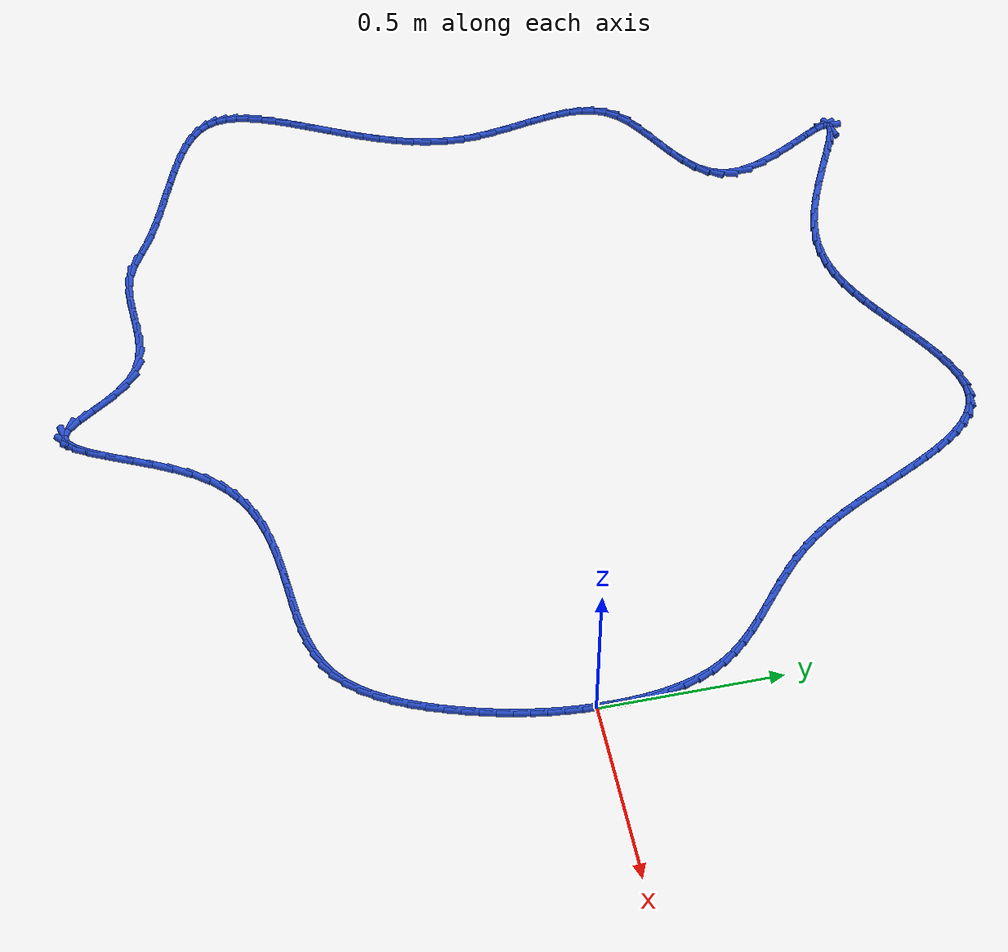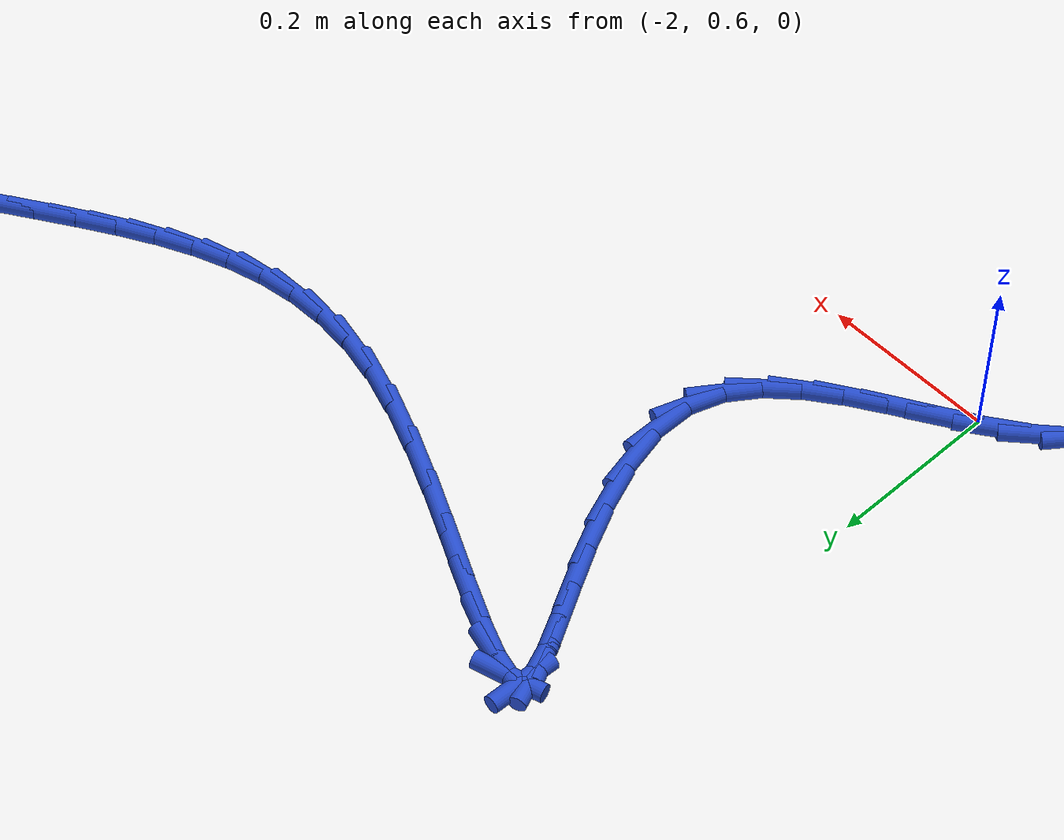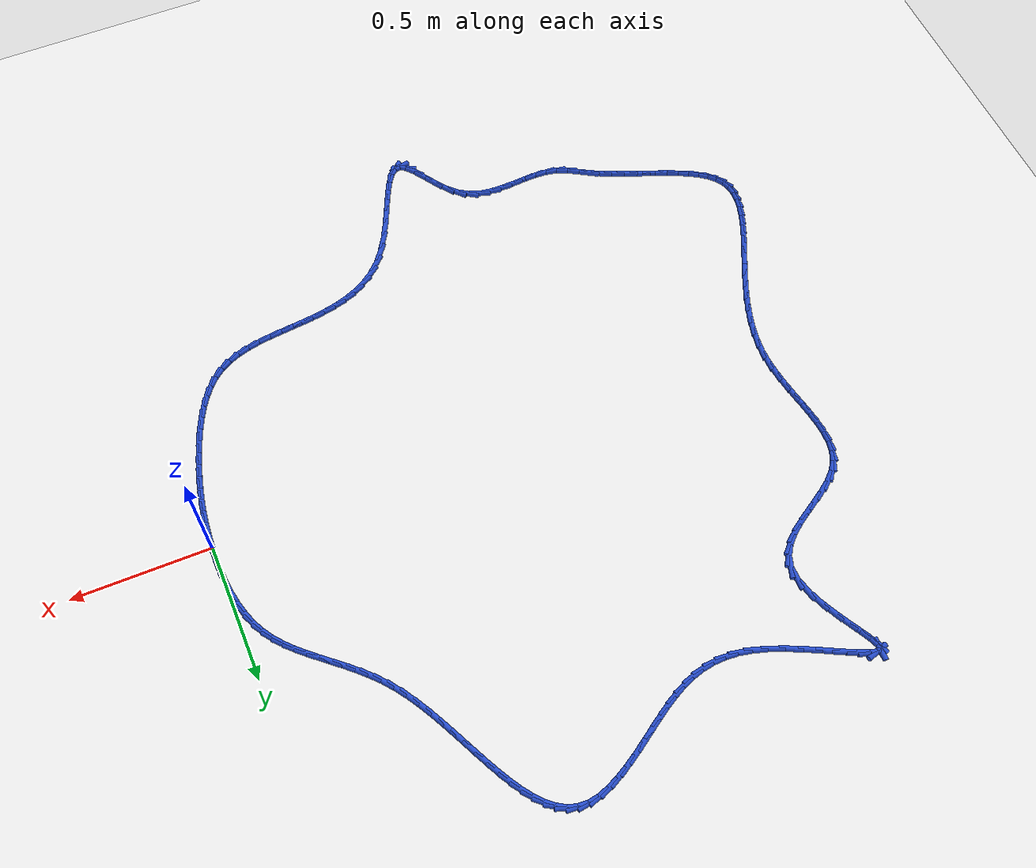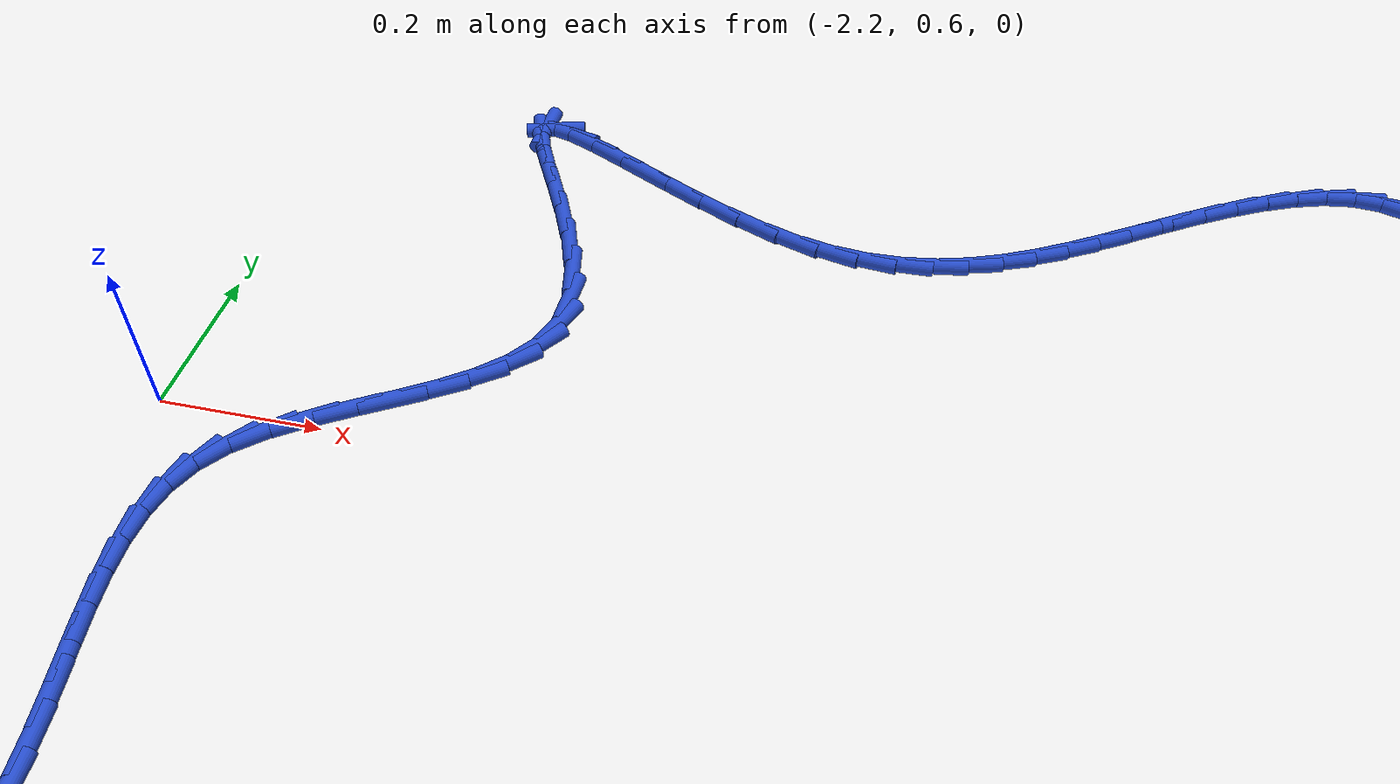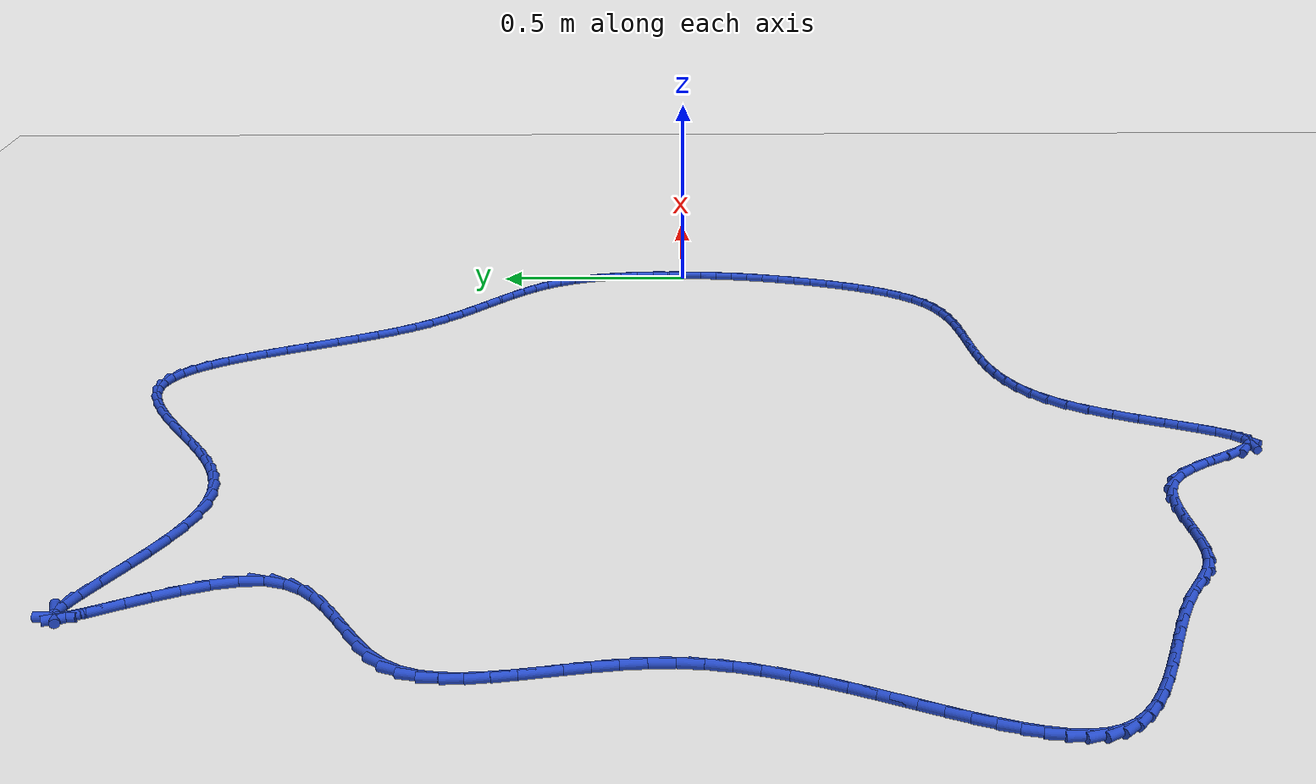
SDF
<sdf version="1.6">
 <world name="default">
  <light name="sun" type="directional">
   <pose>0 0 10 0 -0 0</pose>
   <diffuse>0.8 0.8 0.8 1</diffuse>
   <specular>0.2 0.2 0.2 1</specular>
   <attenuation>
    <range>1000</range>
    <constant>0.9</constant>
    <linear>0.01</linear>
    <quadratic>0.001</quadratic>
   </attenuation>
   <direction>-0.5 0.1 -0.9</direction>
  </light>
  <model name="ground_plane">
   <static>1</static>
   <link name="link">
    <collision name="collision">
     <geometry><plane><normal>0 0 1</normal><size>100 100</size></plane></geometry>
     <surface><friction><ode><mu>100</mu><mu2>50</mu2></ode></friction></surface>
    </collision>
    <visual name="visual">
     <cast_shadows>0</cast_shadows>
     <geometry><plane><normal>0 0 1</normal><size>100 100</size></plane></geometry>
     <material>
      <script><uri>file://media/materials/scripts/gazebo.material</uri><name>Gazebo/WhiteGlow</name></script>
     </material>
    </visual>
   </link>
  </model>
  <gravity>0 0 -9.8</gravity>
  <magnetic_field>6e-06 2.3e-05 -4.2e-05</magnetic_field>
  <atmosphere type="adiabatic"/>
  <physics name="default_physics" default="0" type="ode">
   <max_step_size>0.001</max_step_size>
   <real_time_factor>1</real_time_factor>
   <real_time_update_rate>1000</real_time_update_rate>
  </physics>
  <scene><ambient>0.4 0.4 0.4 1</ambient><background>0.7 0.7 0.7 1</background><shadows>1</shadows></scene>
  <spherical_coordinates>
   <surface_model>EARTH_WGS84</surface_model>
   <latitude_deg>0</latitude_deg>
   <longitude_deg>0</longitude_deg>
   <elevation>0</elevation>
   <heading_deg>0</heading_deg>
  </spherical_coordinates>
  <model name="line">
   <link name="link_0">
    <pose>1.734723475976807e-17 -1.3877787807814457e-17 0.01 0 1.57 1.5534646225807065</pose>
    <collision name="collision">
     <geometry><cylinder><radius>0.01</radius><length>0.08</length></cylinder></geometry>
    </collision>
    <visual name="visual">
     <material>
      <script><name>Gazebo/Blue</name><uri>file://media/materials/scripts/gazebo.material</uri></script>
     </material>
     <geometry><cylinder><radius>0.01</radius><length>0.08</length></cylinder></geometry>
    </visual>
   </link>
   <link name="link_1">
    <pose>0.0007905198224604647 0.04560663261336693 0.01 0 1.57 -1.547656428910895</pose>
    <collision name="collision">
     <geometry><cylinder><radius>0.01</radius><length>0.08</length></cylinder></geometry>
    </collision>
    <visual name="visual">
     <material>
      <script><name>Gazebo/Blue</name><uri>file://media/materials/scripts/gazebo.material</uri></script>
     </material>
     <geometry><cylinder><radius>0.01</radius><length>0.08</length></cylinder></geometry>
    </visual>
   </link>
   <link name="link_2">
    <pose>-0.00027487836473895756 0.09164002602763777 0.01 0 1.57 -1.5004070499833655</pose>
    <collision name="collision">
     <geometry><cylinder><radius>0.01</radius><length>0.08</length></cylinder></geometry>
    </collision>
    <visual name="visual">
     <material>
      <script><name>Gazebo/Blue</name><uri>file://media/materials/scripts/gazebo.material</uri></script>
     </material>
     <geometry><cylinder><radius>0.01</radius><length>0.08</length></cylinder></geometry>
    </visual>
   </link>
   <link name="link_3">
    <pose>-0.0035137321763687485 0.1375774622547021 0.01 0 1.57 -1.4450293220916655</pose>
    <collision name="collision">
     <geometry><cylinder><radius>0.01</radius><length>0.08</length></cylinder></geometry>
    </collision>
    <visual name="visual">
     <material>
      <script><name>Gazebo/Blue</name><uri>file://media/materials/scripts/gazebo.material</uri></script>
     </material>
     <geometry><cylinder><radius>0.01</radius><length>0.08</length></cylinder></geometry>
    </visual>
   </link>
   <link name="link_4">
    <pose>-0.009243579227199396 0.18289622330644942 0.01 0 1.57 -1.3798754588883804</pose>
    <collision name="collision">
     <geometry><cylinder><radius>0.01</radius><length>0.08</length></cylinder></geometry>
    </collision>
    <visual name="visual">
     <material>
      <script><name>Gazebo/Blue</name><uri>file://media/materials/scripts/gazebo.material</uri></script>
     </material>
     <geometry><cylinder><radius>0.01</radius><length>0.08</length></cylinder></geometry>
    </visual>
   </link>
   <link name="link_5">
    <pose>-0.017781957132001397 0.2270735911947691 0.01 0 1.57 -1.3030140759514017</pose>
    <collision name="collision">
     <geometry><cylinder><radius>0.01</radius><length>0.08</length></cylinder></geometry>
    </collision>
    <visual name="visual">
     <material>
      <script><name>Gazebo/Blue</name><uri>file://media/materials/scripts/gazebo.material</uri></script>
     </material>
     <geometry><cylinder><radius>0.01</radius><length>0.08</length></cylinder></geometry>
    </visual>
   </link>
   <link name="link_6">
    <pose>-0.029446403505545247 0.26958684793155085 0.01 0 1.57 -1.2123378392488025</pose>
    <collision name="collision">
     <geometry><cylinder><radius>0.01</radius><length>0.08</length></cylinder></geometry>
    </collision>
    <visual name="visual">
     <material>
      <script><name>Gazebo/Blue</name><uri>file://media/materials/scripts/gazebo.material</uri></script>
     </material>
     <geometry><cylinder><radius>0.01</radius><length>0.08</length></cylinder></geometry>
    </visual>
   </link>
   <link name="link_7">
    <pose>-0.044554455962601436 0.3099132755286841 0.01 0 1.57 -1.1058755438783705</pose>
    <collision name="collision">
     <geometry><cylinder><radius>0.01</radius><length>0.08</length></cylinder></geometry>
    </collision>
    <visual name="visual">
     <material>
      <script><name>Gazebo/Blue</name><uri>file://media/materials/scripts/gazebo.material</uri></script>
     </material>
     <geometry><cylinder><radius>0.01</radius><length>0.08</length></cylinder></geometry>
    </visual>
   </link>
   <link name="link_8">
    <pose>-0.06342313443116523 0.34753082193411133 0.01 0 1.57 -0.9907278969704408</pose>
    <collision name="collision">
     <geometry><cylinder><radius>0.01</radius><length>0.08</length></cylinder></geometry>
    </collision>
    <visual name="visual">
     <material>
      <script><name>Gazebo/Blue</name><uri>file://media/materials/scripts/gazebo.material</uri></script>
     </material>
     <geometry><cylinder><radius>0.01</radius><length>0.08</length></cylinder></geometry>
    </visual>
   </link>
   <link name="link_9">
    <pose>-0.08614484871546925 0.38220636652388984 0.01 0 1.57 -0.8903932539267831</pose>
    <collision name="collision">
     <geometry><cylinder><radius>0.01</radius><length>0.08</length></cylinder></geometry>
    </collision>
    <visual name="visual">
     <material>
      <script><name>Gazebo/Blue</name><uri>file://media/materials/scripts/gazebo.material</uri></script>
     </material>
     <geometry><cylinder><radius>0.01</radius><length>0.08</length></cylinder></geometry>
    </visual>
   </link>
   <link name="link_10">
    <pose>-0.11223732752382055 0.41444604043608474 0.01 0 1.57 -0.8112891752636585</pose>
    <collision name="collision">
     <geometry><cylinder><radius>0.01</radius><length>0.08</length></cylinder></geometry>
    </collision>
    <visual name="visual">
     <material>
      <script><name>Gazebo/Blue</name><uri>file://media/materials/scripts/gazebo.material</uri></script>
     </material>
     <geometry><cylinder><radius>0.01</radius><length>0.08</length></cylinder></geometry>
    </visual>
   </link>
   <link name="link_11">
    <pose>-0.14112769551556953 0.4448725250194977 0.01 0 1.57 -0.7542671647679721</pose>
    <collision name="collision">
     <geometry><cylinder><radius>0.01</radius><length>0.08</length></cylinder></geometry>
    </collision>
    <visual name="visual">
     <material>
      <script><name>Gazebo/Blue</name><uri>file://media/materials/scripts/gazebo.material</uri></script>
     </material>
     <geometry><cylinder><radius>0.01</radius><length>0.08</length></cylinder></geometry>
    </visual>
   </link>
   <link name="link_12">
    <pose>-0.17224307735006647 0.4741085016229301 0.01 0 1.57 -0.7187707049857153</pose>
    <collision name="collision">
     <geometry><cylinder><radius>0.01</radius><length>0.08</length></cylinder></geometry>
    </collision>
    <visual name="visual">
     <material>
      <script><name>Gazebo/Blue</name><uri>file://media/materials/scripts/gazebo.material</uri></script>
     </material>
     <geometry><cylinder><radius>0.01</radius><length>0.08</length></cylinder></geometry>
    </visual>
   </link>
   <link name="link_13">
    <pose>-0.20501059768666172 0.5027766515951835 0.01 0 1.57 -0.7036914518162153</pose>
    <collision name="collision">
     <geometry><cylinder><radius>0.01</radius><length>0.08</length></cylinder></geometry>
    </collision>
    <visual name="visual">
     <material>
      <script><name>Gazebo/Blue</name><uri>file://media/materials/scripts/gazebo.material</uri></script>
     </material>
     <geometry><cylinder><radius>0.01</radius><length>0.08</length></cylinder></geometry>
    </visual>
   </link>
   <link name="link_14">
    <pose>-0.2388573811847056 0.5314996562850592 0.01 0 1.57 -0.7078700688933969</pose>
    <collision name="collision">
     <geometry><cylinder><radius>0.01</radius><length>0.08</length></cylinder></geometry>
    </collision>
    <visual name="visual">
     <material>
      <script><name>Gazebo/Blue</name><uri>file://media/materials/scripts/gazebo.material</uri></script>
     </material>
     <geometry><cylinder><radius>0.01</radius><length>0.08</length></cylinder></geometry>
    </visual>
   </link>
   <link name="link_15">
    <pose>-0.2732105525035486 0.5609001970413593 0.01 0 1.57 -0.730275314983436</pose>
    <collision name="collision">
     <geometry><cylinder><radius>0.01</radius><length>0.08</length></cylinder></geometry>
    </collision>
    <visual name="visual">
     <material>
      <script><name>Gazebo/Blue</name><uri>file://media/materials/scripts/gazebo.material</uri></script>
     </material>
     <geometry><cylinder><radius>0.01</radius><length>0.08</length></cylinder></geometry>
    </visual>
   </link>
   <link name="link_16">
    <pose>-0.3074972363025406 0.5916009552128846 0.01 0 1.57 -0.7699527507529377</pose>
    <collision name="collision">
     <geometry><cylinder><radius>0.01</radius><length>0.08</length></cylinder></geometry>
    </collision>
    <visual name="visual">
     <material>
      <script><name>Gazebo/Blue</name><uri>file://media/materials/scripts/gazebo.material</uri></script>
     </material>
     <geometry><cylinder><radius>0.01</radius><length>0.08</length></cylinder></geometry>
    </visual>
   </link>
   <link name="link_17">
    <pose>-0.34114455724103243 0.624224612148437 0.01 0 1.57 -0.8258196194710178</pose>
    <collision name="collision">
     <geometry><cylinder><radius>0.01</radius><length>0.08</length></cylinder></geometry>
    </collision>
    <visual name="visual">
     <material>
      <script><name>Gazebo/Blue</name><uri>file://media/materials/scripts/gazebo.material</uri></script>
     </material>
     <geometry><cylinder><radius>0.01</radius><length>0.08</length></cylinder></geometry>
    </visual>
   </link>
   <link name="link_18">
    <pose>-0.3735796399783743 0.6593938491968183 0.01 0 1.57 -0.8962778897993412</pose>
    <collision name="collision">
     <geometry><cylinder><radius>0.01</radius><length>0.08</length></cylinder></geometry>
    </collision>
    <visual name="visual">
     <material>
      <script><name>Gazebo/Blue</name><uri>file://media/materials/scripts/gazebo.material</uri></script>
     </material>
     <geometry><cylinder><radius>0.01</radius><length>0.08</length></cylinder></geometry>
    </visual>
   </link>
   <link name="link_19">
    <pose>-0.4042323166619555 0.6977271771397399 0.01 0 1.57 -0.9694761312723835</pose>
    <collision name="collision">
     <geometry><cylinder><radius>0.01</radius><length>0.08</length></cylinder></geometry>
    </collision>
    <visual name="visual">
     <material>
      <script><name>Gazebo/Blue</name><uri>file://media/materials/scripts/gazebo.material</uri></script>
     </material>
     <geometry><cylinder><radius>0.01</radius><length>0.08</length></cylinder></geometry>
    </visual>
   </link>
   <link name="link_20">
    <pose>-0.43282153255997163 0.7393977619783605 0.01 0 1.57 -1.0274167699275776</pose>
    <collision name="collision">
     <geometry><cylinder><radius>0.01</radius><length>0.08</length></cylinder></geometry>
    </collision>
    <visual name="visual">
     <material>
      <script><name>Gazebo/Blue</name><uri>file://media/materials/scripts/gazebo.material</uri></script>
     </material>
     <geometry><cylinder><radius>0.01</radius><length>0.08</length></cylinder></geometry>
    </visual>
   </link>
   <link name="link_21">
    <pose>-0.4596081361703791 0.7837440314831149 0.01 0 1.57 -1.0703333471950411</pose>
    <collision name="collision">
     <geometry><cylinder><radius>0.01</radius><length>0.08</length></cylinder></geometry>
    </collision>
    <visual name="visual">
     <material>
      <script><name>Gazebo/Blue</name><uri>file://media/materials/scripts/gazebo.material</uri></script>
     </material>
     <geometry><cylinder><radius>0.01</radius><length>0.08</length></cylinder></geometry>
    </visual>
   </link>
   <link name="link_22">
    <pose>-0.4849125866131583 0.8300125902677802 0.01 0 1.57 -1.1000233403745476</pose>
    <collision name="collision">
     <geometry><cylinder><radius>0.01</radius><length>0.08</length></cylinder></geometry>
    </collision>
    <visual name="visual">
     <material>
      <script><name>Gazebo/Blue</name><uri>file://media/materials/scripts/gazebo.material</uri></script>
     </material>
     <geometry><cylinder><radius>0.01</radius><length>0.08</length></cylinder></geometry>
    </visual>
   </link>
   <link name="link_23">
    <pose>-0.5090553430082895 0.877450042946133 0.01 0 1.57 -1.1176511071005621</pose>
    <collision name="collision">
     <geometry><cylinder><radius>0.01</radius><length>0.08</length></cylinder></geometry>
    </collision>
    <visual name="visual">
     <material>
      <script><name>Gazebo/Blue</name><uri>file://media/materials/scripts/gazebo.material</uri></script>
     </material>
     <geometry><cylinder><radius>0.01</radius><length>0.08</length></cylinder></geometry>
    </visual>
   </link>
   <link name="link_24">
    <pose>-0.5323568644757519 0.9253029941319498 0.01 0 1.57 -1.1237293968194622</pose>
    <collision name="collision">
     <geometry><cylinder><radius>0.01</radius><length>0.08</length></cylinder></geometry>
    </collision>
    <visual name="visual">
     <material>
      <script><name>Gazebo/Blue</name><uri>file://media/materials/scripts/gazebo.material</uri></script>
     </material>
     <geometry><cylinder><radius>0.01</radius><length>0.08</length></cylinder></geometry>
    </visual>
   </link>
   <link name="link_25">
    <pose>-0.555137610135527 0.9728180484390083 0.01 0 1.57 -1.1180893407142427</pose>
    <collision name="collision">
     <geometry><cylinder><radius>0.01</radius><length>0.08</length></cylinder></geometry>
    </collision>
    <visual name="visual">
     <material>
      <script><name>Gazebo/Blue</name><uri>file://media/materials/scripts/gazebo.material</uri></script>
     </material>
     <geometry><cylinder><radius>0.01</radius><length>0.08</length></cylinder></geometry>
    </visual>
   </link>
   <link name="link_26">
    <pose>-0.577718039107594 1.019241810481085 0.01 0 1.57 -1.0997996830753136</pose>
    <collision name="collision">
     <geometry><cylinder><radius>0.01</radius><length>0.08</length></cylinder></geometry>
    </collision>
    <visual name="visual">
     <material>
      <script><name>Gazebo/Blue</name><uri>file://media/materials/scripts/gazebo.material</uri></script>
     </material>
     <geometry><cylinder><radius>0.01</radius><length>0.08</length></cylinder></geometry>
    </visual>
   </link>
   <link name="link_27">
    <pose>-0.6004186105119333 1.063820884871956 0.01 0 1.57 -1.0670094312827587</pose>
    <collision name="collision">
     <geometry><cylinder><radius>0.01</radius><length>0.08</length></cylinder></geometry>
    </collision>
    <visual name="visual">
     <material>
      <script><name>Gazebo/Blue</name><uri>file://media/materials/scripts/gazebo.material</uri></script>
     </material>
     <geometry><cylinder><radius>0.01</radius><length>0.08</length></cylinder></geometry>
    </visual>
   </link>
   <link name="link_28">
    <pose>-0.6235597834685254 1.1058018762253994 0.01 0 1.57 -1.0166998579384672</pose>
    <collision name="collision">
     <geometry><cylinder><radius>0.01</radius><length>0.08</length></cylinder></geometry>
    </collision>
    <visual name="visual">
     <material>
      <script><name>Gazebo/Blue</name><uri>file://media/materials/scripts/gazebo.material</uri></script>
     </material>
     <geometry><cylinder><radius>0.01</radius><length>0.08</length></cylinder></geometry>
    </visual>
   </link>
   <link name="link_29">
    <pose>-0.6474620170973501 1.1444313891551914 0.01 0 1.57 -0.9443736174853934</pose>
    <collision name="collision">
     <geometry><cylinder><radius>0.01</radius><length>0.08</length></cylinder></geometry>
    </collision>
    <visual name="visual">
     <material>
      <script><name>Gazebo/Blue</name><uri>file://media/materials/scripts/gazebo.material</uri></script>
     </material>
     <geometry><cylinder><radius>0.01</radius><length>0.08</length></cylinder></geometry>
    </visual>
   </link>
   <link name="link_30">
    <pose>-0.6724457705183875 1.1789560282751084 0.01 0 1.57 -0.8438598289288278</pose>
    <collision name="collision">
     <geometry><cylinder><radius>0.01</radius><length>0.08</length></cylinder></geometry>
    </collision>
    <visual name="visual">
     <material>
      <script><name>Gazebo/Blue</name><uri>file://media/materials/scripts/gazebo.material</uri></script>
     </material>
     <geometry><cylinder><radius>0.01</radius><length>0.08</length></cylinder></geometry>
    </visual>
   </link>
   <link name="link_31">
    <pose>-0.6988315028516178 1.2086223981989281 0.01 0 1.57 -0.7078461603763037</pose>
    <collision name="collision">
     <geometry><cylinder><radius>0.01</radius><length>0.08</length></cylinder></geometry>
    </collision>
    <visual name="visual">
     <material>
      <script><name>Gazebo/Blue</name><uri>file://media/materials/scripts/gazebo.material</uri></script>
     </material>
     <geometry><cylinder><radius>0.01</radius><length>0.08</length></cylinder></geometry>
    </visual>
   </link>
   <link name="link_32">
    <pose>-0.7269396732170214 1.2326771035404265 0.01 0 1.57 -0.5305830318928488</pose>
    <collision name="collision">
     <geometry><cylinder><radius>0.01</radius><length>0.08</length></cylinder></geometry>
    </collision>
    <visual name="visual">
     <material>
      <script><name>Gazebo/Blue</name><uri>file://media/materials/scripts/gazebo.material</uri></script>
     </material>
     <geometry><cylinder><radius>0.01</radius><length>0.08</length></cylinder></geometry>
    </visual>
   </link>
   <link name="link_33">
    <pose>-0.7570907407345782 1.2503667489133812 0.01 0 1.57 -0.3143432281464041</pose>
    <collision name="collision">
     <geometry><cylinder><radius>0.01</radius><length>0.08</length></cylinder></geometry>
    </collision>
    <visual name="visual">
     <material>
      <script><name>Gazebo/Blue</name><uri>file://media/materials/scripts/gazebo.material</uri></script>
     </material>
     <geometry><cylinder><radius>0.01</radius><length>0.08</length></cylinder></geometry>
    </visual>
   </link>
   <link name="link_34">
    <pose>-0.7896051645242681 1.2609379389315687 0.01 0 1.57 -0.07654279052104714</pose>
    <collision name="collision">
     <geometry><cylinder><radius>0.01</radius><length>0.08</length></cylinder></geometry>
    </collision>
    <visual name="visual">
     <material>
      <script><name>Gazebo/Blue</name><uri>file://media/materials/scripts/gazebo.material</uri></script>
     </material>
     <geometry><cylinder><radius>0.01</radius><length>0.08</length></cylinder></geometry>
    </visual>
   </link>
   <link name="link_35">
    <pose>-0.8248033536605607 1.263637380437805 0.01 0 1.57 0.14318964473658882</pose>
    <collision name="collision">
     <geometry><cylinder><radius>0.01</radius><length>0.08</length></cylinder></geometry>
    </collision>
    <visual name="visual">
     <material>
      <script><name>Gazebo/Blue</name><uri>file://media/materials/scripts/gazebo.material</uri></script>
     </material>
     <geometry><cylinder><radius>0.01</radius><length>0.08</length></cylinder></geometry>
    </visual>
   </link>
   <link name="link_36">
    <pose>-0.8627856947542022 1.258161224879412 0.01 0 1.57 0.3013100866943954</pose>
    <collision name="collision">
     <geometry><cylinder><radius>0.01</radius><length>0.08</length></cylinder></geometry>
    </collision>
    <visual name="visual">
     <material>
      <script><name>Gazebo/Blue</name><uri>file://media/materials/scripts/gazebo.material</uri></script>
     </material>
     <geometry><cylinder><radius>0.01</radius><length>0.08</length></cylinder></geometry>
    </visual>
   </link>
   <link name="link_37">
    <pose>-0.9029277795782182 1.2456861776602348 0.01 0 1.57 0.40885046792092133</pose>
    <collision name="collision">
     <geometry><cylinder><radius>0.01</radius><length>0.08</length></cylinder></geometry>
    </collision>
    <visual name="visual">
     <material>
      <script><name>Gazebo/Blue</name><uri>file://media/materials/scripts/gazebo.material</uri></script>
     </material>
     <geometry><cylinder><radius>0.01</radius><length>0.08</length></cylinder></geometry>
    </visual>
   </link>
   <link name="link_38">
    <pose>-0.9444561697568606 1.2276933712646212 0.01 0 1.57 0.4816832215368371</pose>
    <collision name="collision">
     <geometry><cylinder><radius>0.01</radius><length>0.08</length></cylinder></geometry>
    </collision>
    <visual name="visual">
     <material>
      <script><name>Gazebo/Blue</name><uri>file://media/materials/scripts/gazebo.material</uri></script>
     </material>
     <geometry><cylinder><radius>0.01</radius><length>0.08</length></cylinder></geometry>
    </visual>
   </link>
   <link name="link_39">
    <pose>-0.9865974269143802 1.2056639381769156 0.01 0 1.57 0.5297823782529048</pose>
    <collision name="collision">
     <geometry><cylinder><radius>0.01</radius><length>0.08</length></cylinder></geometry>
    </collision>
    <visual name="visual">
     <material>
      <script><name>Gazebo/Blue</name><uri>file://media/materials/scripts/gazebo.material</uri></script>
     </material>
     <geometry><cylinder><radius>0.01</radius><length>0.08</length></cylinder></geometry>
    </visual>
   </link>
   <link name="link_40">
    <pose>-1.028578112675028 1.181079010881465 0.01 0 1.57 0.5587077497362689</pose>
    <collision name="collision">
     <geometry><cylinder><radius>0.01</radius><length>0.08</length></cylinder></geometry>
    </collision>
    <visual name="visual">
     <material>
      <script><name>Gazebo/Blue</name><uri>file://media/materials/scripts/gazebo.material</uri></script>
     </material>
     <geometry><cylinder><radius>0.01</radius><length>0.08</length></cylinder></geometry>
    </visual>
   </link>
   <link name="link_41">
    <pose>-1.069643423239414 1.1554069990560547 0.01 0 1.57 0.5711012610190326</pose>
    <collision name="collision">
     <geometry><cylinder><radius>0.01</radius><length>0.08</length></cylinder></geometry>
    </collision>
    <visual name="visual">
     <material>
      <script><name>Gazebo/Blue</name><uri>file://media/materials/scripts/gazebo.material</uri></script>
     </material>
     <geometry><cylinder><radius>0.01</radius><length>0.08</length></cylinder></geometry>
    </visual>
   </link>
   <link name="link_42">
    <pose>-1.1095756104811645 1.1297496361895816 0.01 0 1.57 0.5670435959536316</pose>
    <collision name="collision">
     <geometry><cylinder><radius>0.01</radius><length>0.08</length></cylinder></geometry>
    </collision>
    <visual name="visual">
     <material>
      <script><name>Gazebo/Blue</name><uri>file://media/materials/scripts/gazebo.material</uri></script>
     </material>
     <geometry><cylinder><radius>0.01</radius><length>0.08</length></cylinder></geometry>
    </visual>
   </link>
   <link name="link_43">
    <pose>-1.1487621929503096 1.1047954083381095 0.01 0 1.57 0.5454784414288211</pose>
    <collision name="collision">
     <geometry><cylinder><radius>0.01</radius><length>0.08</length></cylinder></geometry>
    </collision>
    <visual name="visual">
     <material>
      <script><name>Gazebo/Blue</name><uri>file://media/materials/scripts/gazebo.material</uri></script>
     </material>
     <geometry><cylinder><radius>0.01</radius><length>0.08</length></cylinder></geometry>
    </visual>
   </link>
   <link name="link_44">
    <pose>-1.1876230271420563 1.081210722739638 0.01 0 1.57 0.5052743356407918</pose>
    <collision name="collision">
     <geometry><cylinder><radius>0.01</radius><length>0.08</length></cylinder></geometry>
    </collision>
    <visual name="visual">
     <material>
      <script><name>Gazebo/Blue</name><uri>file://media/materials/scripts/gazebo.material</uri></script>
     </material>
     <geometry><cylinder><radius>0.01</radius><length>0.08</length></cylinder></geometry>
    </visual>
   </link>
   <link name="link_45">
    <pose>-1.2265779695516135 1.0596619866321677 0.01 0 1.57 0.4454856443325451</pose>
    <collision name="collision">
     <geometry><cylinder><radius>0.01</radius><length>0.08</length></cylinder></geometry>
    </collision>
    <visual name="visual">
     <material>
      <script><name>Gazebo/Blue</name><uri>file://media/materials/scripts/gazebo.material</uri></script>
     </material>
     <geometry><cylinder><radius>0.01</radius><length>0.08</length></cylinder></geometry>
    </visual>
   </link>
   <link name="link_46">
    <pose>-1.2660468766741888 1.0408156072536976 0.01 0 1.57 0.3658386041662883</pose>
    <collision name="collision">
     <geometry><cylinder><radius>0.01</radius><length>0.08</length></cylinder></geometry>
    </collision>
    <visual name="visual">
     <material>
      <script><name>Gazebo/Blue</name><uri>file://media/materials/scripts/gazebo.material</uri></script>
     </material>
     <geometry><cylinder><radius>0.01</radius><length>0.08</length></cylinder></geometry>
    </visual>
   </link>
   <link name="link_47">
    <pose>-1.3064496050049892 1.0253379918422278 0.01 0 1.57 0.26746276634169214</pose>
    <collision name="collision">
     <geometry><cylinder><radius>0.01</radius><length>0.08</length></cylinder></geometry>
    </collision>
    <visual name="visual">
     <material>
      <script><name>Gazebo/Blue</name><uri>file://media/materials/scripts/gazebo.material</uri></script>
     </material>
     <geometry><cylinder><radius>0.01</radius><length>0.08</length></cylinder></geometry>
    </visual>
   </link>
   <link name="link_48">
    <pose>-1.3482060110392238 1.0138955476357587 0.01 0 1.57 0.15363552604569491</pose>
    <collision name="collision">
     <geometry><cylinder><radius>0.01</radius><length>0.08</length></cylinder></geometry>
    </collision>
    <visual name="visual">
     <material>
      <script><name>Gazebo/Blue</name><uri>file://media/materials/scripts/gazebo.material</uri></script>
     </material>
     <geometry><cylinder><radius>0.01</radius><length>0.08</length></cylinder></geometry>
    </visual>
   </link>
   <link name="link_49">
    <pose>-1.3917359512721001 1.0071546818722896 0.01 0 1.57 0.03001679240443435</pose>
    <collision name="collision">
     <geometry><cylinder><radius>0.01</radius><length>0.08</length></cylinder></geometry>
    </collision>
    <visual name="visual">
     <material>
      <script><name>Gazebo/Blue</name><uri>file://media/materials/scripts/gazebo.material</uri></script>
     </material>
     <geometry><cylinder><radius>0.01</radius><length>0.08</length></cylinder></geometry>
    </visual>
   </link>
   <link name="link_50">
    <pose>-1.4374592821988257 1.0057818017898206 0.01 0 1.57 -0.09614130344304528</pose>
    <collision name="collision">
     <geometry><cylinder><radius>0.01</radius><length>0.08</length></cylinder></geometry>
    </collision>
    <visual name="visual">
     <material>
      <script><name>Gazebo/Blue</name><uri>file://media/materials/scripts/gazebo.material</uri></script>
     </material>
     <geometry><cylinder><radius>0.01</radius><length>0.08</length></cylinder></geometry>
    </visual>
   </link>
   <link name="link_51">
    <pose>-1.4857958603146082 1.010443314626352 0.01 0 1.57 -0.217616136208942</pose>
    <collision name="collision">
     <geometry><cylinder><radius>0.01</radius><length>0.08</length></cylinder></geometry>
    </collision>
    <visual name="visual">
     <material>
      <script><name>Gazebo/Blue</name><uri>file://media/materials/scripts/gazebo.material</uri></script>
     </material>
     <geometry><cylinder><radius>0.01</radius><length>0.08</length></cylinder></geometry>
    </visual>
   </link>
   <link name="link_52">
    <pose>-1.5371620856071457 1.0218012951915747 0.01 0 1.57 -0.31934479748372185</pose>
    <collision name="collision">
     <geometry><cylinder><radius>0.01</radius><length>0.08</length></cylinder></geometry>
    </collision>
    <visual name="visual">
     <material>
      <script><name>Gazebo/Blue</name><uri>file://media/materials/scripts/gazebo.material</uri></script>
     </material>
     <geometry><cylinder><radius>0.01</radius><length>0.08</length></cylinder></geometry>
    </visual>
   </link>
   <link name="link_53">
    <pose>-1.5913326182944183 1.03971345390816 0.01 0 1.57 -0.387315112144202</pose>
    <collision name="collision">
     <geometry><cylinder><radius>0.01</radius><length>0.08</length></cylinder></geometry>
    </collision>
    <visual name="visual">
     <material>
      <script><name>Gazebo/Blue</name><uri>file://media/materials/scripts/gazebo.material</uri></script>
     </material>
     <geometry><cylinder><radius>0.01</radius><length>0.08</length></cylinder></geometry>
    </visual>
   </link>
   <link name="link_54">
    <pose>-1.6466926309231027 1.062295900550445 0.01 0 1.57 -0.43045717931309174</pose>
    <collision name="collision">
     <geometry><cylinder><radius>0.01</radius><length>0.08</length></cylinder></geometry>
    </collision>
    <visual name="visual">
     <material>
      <script><name>Gazebo/Blue</name><uri>file://media/materials/scripts/gazebo.material</uri></script>
     </material>
     <geometry><cylinder><radius>0.01</radius><length>0.08</length></cylinder></geometry>
    </visual>
   </link>
   <link name="link_55">
    <pose>-1.7014456777028946 1.0874371022731395 0.01 0 1.57 -0.45464633257627995</pose>
    <collision name="collision">
     <geometry><cylinder><radius>0.01</radius><length>0.08</length></cylinder></geometry>
    </collision>
    <visual name="visual">
     <material>
      <script><name>Gazebo/Blue</name><uri>file://media/materials/scripts/gazebo.material</uri></script>
     </material>
     <geometry><cylinder><radius>0.01</radius><length>0.08</length></cylinder></geometry>
    </visual>
   </link>
   <link name="link_56">
    <pose>-1.753795312843489 1.1130255262309527 0.01 0 1.57 -0.46113936427236935</pose>
    <collision name="collision">
     <geometry><cylinder><radius>0.01</radius><length>0.08</length></cylinder></geometry>
    </collision>
    <visual name="visual">
     <material>
      <script><name>Gazebo/Blue</name><uri>file://media/materials/scripts/gazebo.material</uri></script>
     </material>
     <geometry><cylinder><radius>0.01</radius><length>0.08</length></cylinder></geometry>
    </visual>
   </link>
   <link name="link_57">
    <pose>-1.8019450905545826 1.1369496395785958 0.01 0 1.57 -0.44587215320055135</pose>
    <collision name="collision">
     <geometry><cylinder><radius>0.01</radius><length>0.08</length></cylinder></geometry>
    </collision>
    <visual name="visual">
     <material>
      <script><name>Gazebo/Blue</name><uri>file://media/materials/scripts/gazebo.material</uri></script>
     </material>
     <geometry><cylinder><radius>0.01</radius><length>0.08</length></cylinder></geometry>
    </visual>
   </link>
   <link name="link_58">
    <pose>-1.8440985650458723 1.1570979094707785 0.01 0 1.57 -0.39339976792522097</pose>
    <collision name="collision">
     <geometry><cylinder><radius>0.01</radius><length>0.08</length></cylinder></geometry>
    </collision>
    <visual name="visual">
     <material>
      <script><name>Gazebo/Blue</name><uri>file://media/materials/scripts/gazebo.material</uri></script>
     </material>
     <geometry><cylinder><radius>0.01</radius><length>0.08</length></cylinder></geometry>
    </visual>
   </link>
   <link name="link_59">
    <pose>-1.8784592905270527 1.1713588030622109 0.01 0 1.57 -0.24760240715004062</pose>
    <collision name="collision">
     <geometry><cylinder><radius>0.01</radius><length>0.08</length></cylinder></geometry>
    </collision>
    <visual name="visual">
     <material>
      <script><name>Gazebo/Blue</name><uri>file://media/materials/scripts/gazebo.material</uri></script>
     </material>
     <geometry><cylinder><radius>0.01</radius><length>0.08</length></cylinder></geometry>
    </visual>
   </link>
   <link name="link_60">
    <pose>-1.9032308212078206 1.1776207875076032 0.01 0 1.57 0.2799507985611413</pose>
    <collision name="collision">
     <geometry><cylinder><radius>0.01</radius><length>0.08</length></cylinder></geometry>
    </collision>
    <visual name="visual">
     <material>
      <script><name>Gazebo/Blue</name><uri>file://media/materials/scripts/gazebo.material</uri></script>
     </material>
     <geometry><cylinder><radius>0.01</radius><length>0.08</length></cylinder></geometry>
    </visual>
   </link>
   <link name="link_61">
    <pose>-1.916616711297872 1.1737723299616662 0.01 0 1.57 1.5387954735905094</pose>
    <collision name="collision">
     <geometry><cylinder><radius>0.01</radius><length>0.08</length></cylinder></geometry>
    </collision>
    <visual name="visual">
     <material>
      <script><name>Gazebo/Blue</name><uri>file://media/materials/scripts/gazebo.material</uri></script>
     </material>
     <geometry><cylinder><radius>0.01</radius><length>0.08</length></cylinder></geometry>
    </visual>
   </link>
   <link name="link_62">
    <pose>-1.9171228708050627 1.1579606666339002 0.01 0 1.57 -1.1888984299394942</pose>
    <collision name="collision">
     <geometry><cylinder><radius>0.01</radius><length>0.08</length></cylinder></geometry>
    </collision>
    <visual name="visual">
     <material>
      <script><name>Gazebo/Blue</name><uri>file://media/materials/scripts/gazebo.material</uri></script>
     </material>
     <geometry><cylinder><radius>0.01</radius><length>0.08</length></cylinder></geometry>
    </visual>
   </link>
   <link name="link_63">
    <pose>-1.9062550811095824 1.1309004522660042 0.01 0 1.57 -1.0861761299502208</pose>
    <collision name="collision">
     <geometry><cylinder><radius>0.01</radius><length>0.08</length></cylinder></geometry>
    </collision>
    <visual name="visual">
     <material>
      <script><name>Gazebo/Blue</name><uri>file://media/materials/scripts/gazebo.material</uri></script>
     </material>
     <geometry><cylinder><radius>0.01</radius><length>0.08</length></cylinder></geometry>
    </visual>
   </link>
   <link name="link_64">
    <pose>-1.8872350891223835 1.0947749384685037 0.01 0 1.57 -1.0628668324094037</pose>
    <collision name="collision">
     <geometry><cylinder><radius>0.01</radius><length>0.08</length></cylinder></geometry>
    </collision>
    <visual name="visual">
     <material>
      <script><name>Gazebo/Blue</name><uri>file://media/materials/scripts/gazebo.material</uri></script>
     </material>
     <geometry><cylinder><radius>0.01</radius><length>0.08</length></cylinder></geometry>
    </visual>
   </link>
   <link name="link_65">
    <pose>-1.8633048224129243 1.0517846483246676 0.01 0 1.57 -1.0778563651761286</pose>
    <collision name="collision">
     <geometry><cylinder><radius>0.01</radius><length>0.08</length></cylinder></geometry>
    </collision>
    <visual name="visual">
     <material>
      <script><name>Gazebo/Blue</name><uri>file://media/materials/scripts/gazebo.material</uri></script>
     </material>
     <geometry><cylinder><radius>0.01</radius><length>0.08</length></cylinder></geometry>
    </visual>
   </link>
   <link name="link_66">
    <pose>-1.8377062085506652 1.0041301049177658 0.01 0 1.57 -1.1237911565704752</pose>
    <collision name="collision">
     <geometry><cylinder><radius>0.01</radius><length>0.08</length></cylinder></geometry>
    </collision>
    <visual name="visual">
     <material>
      <script><name>Gazebo/Blue</name><uri>file://media/materials/scripts/gazebo.material</uri></script>
     </material>
     <geometry><cylinder><radius>0.01</radius><length>0.08</length></cylinder></geometry>
    </visual>
   </link>
   <link name="link_67">
    <pose>-1.8136811751050668 0.9540118313310687 0.01 0 1.57 -1.2065300113484516</pose>
    <collision name="collision">
     <geometry><cylinder><radius>0.01</radius><length>0.08</length></cylinder></geometry>
    </collision>
    <visual name="visual">
     <material>
      <script><name>Gazebo/Blue</name><uri>file://media/materials/scripts/gazebo.material</uri></script>
     </material>
     <geometry><cylinder><radius>0.01</radius><length>0.08</length></cylinder></geometry>
    </visual>
   </link>
   <link name="link_68">
    <pose>-1.7944716496455875 0.9036303506478455 0.01 0 1.57 -1.344533228156261</pose>
    <collision name="collision">
     <geometry><cylinder><radius>0.01</radius><length>0.08</length></cylinder></geometry>
    </collision>
    <visual name="visual">
     <material>
      <script><name>Gazebo/Blue</name><uri>file://media/materials/scripts/gazebo.material</uri></script>
     </material>
     <geometry><cylinder><radius>0.01</radius><length>0.08</length></cylinder></geometry>
    </visual>
   </link>
   <link name="link_69">
    <pose>-1.7833195597416875 0.8551861859513658 0.01 0 1.57 1.5677152442393496</pose>
    <collision name="collision">
     <geometry><cylinder><radius>0.01</radius><length>0.08</length></cylinder></geometry>
    </collision>
    <visual name="visual">
     <material>
      <script><name>Gazebo/Blue</name><uri>file://media/materials/scripts/gazebo.material</uri></script>
     </material>
     <geometry><cylinder><radius>0.01</radius><length>0.08</length></cylinder></geometry>
    </visual>
   </link>
   <link name="link_70">
    <pose>-1.783456090132459 0.8108738521274894 0.01 0 1.57 1.2493230273922211</pose>
    <collision name="collision">
     <geometry><cylinder><radius>0.01</radius><length>0.08</length></cylinder></geometry>
    </collision>
    <visual name="visual">
     <material>
      <script><name>Gazebo/Blue</name><uri>file://media/materials/scripts/gazebo.material</uri></script>
     </material>
     <geometry><cylinder><radius>0.01</radius><length>0.08</length></cylinder></geometry>
    </visual>
   </link>
   <link name="link_71">
    <pose>-1.796421352285184 0.7719420889073826 0.01 0 1.57 0.9634943874608078</pose>
    <collision name="collision">
     <geometry><cylinder><radius>0.01</radius><length>0.08</length></cylinder></geometry>
    </collision>
    <visual name="visual">
     <material>
      <script><name>Gazebo/Blue</name><uri>file://media/materials/scripts/gazebo.material</uri></script>
     </material>
     <geometry><cylinder><radius>0.01</radius><length>0.08</length></cylinder></geometry>
    </visual>
   </link>
   <link name="link_72">
    <pose>-1.8202363496381622 0.7376714865659054 0.01 0 1.57 0.7587868849092794</pose>
    <collision name="collision">
     <geometry><cylinder><radius>0.01</radius><length>0.08</length></cylinder></geometry>
    </collision>
    <visual name="visual">
     <material>
      <script><name>Gazebo/Blue</name><uri>file://media/materials/scripts/gazebo.material</uri></script>
     </material>
     <geometry><cylinder><radius>0.01</radius><length>0.08</length></cylinder></geometry>
    </visual>
   </link>
   <link name="link_73">
    <pose>-1.8524829445801707 0.7070970347283357 0.01 0 1.57 0.6291008036097305</pose>
    <collision name="collision">
     <geometry><cylinder><radius>0.01</radius><length>0.08</length></cylinder></geometry>
    </collision>
    <visual name="visual">
     <material>
      <script><name>Gazebo/Blue</name><uri>file://media/materials/scripts/gazebo.material</uri></script>
     </material>
     <geometry><cylinder><radius>0.01</radius><length>0.08</length></cylinder></geometry>
    </visual>
   </link>
   <link name="link_74">
    <pose>-1.8907429994999856 0.6792537230199517 0.01 0 1.57 0.5571818833671177</pose>
    <collision name="collision">
     <geometry><cylinder><radius>0.01</radius><length>0.08</length></cylinder></geometry>
    </collision>
    <visual name="visual">
     <material>
      <script><name>Gazebo/Blue</name><uri>file://media/materials/scripts/gazebo.material</uri></script>
     </material>
     <geometry><cylinder><radius>0.01</radius><length>0.08</length></cylinder></geometry>
    </visual>
   </link>
   <link name="link_75">
    <pose>-1.9325983767863815 0.6531765410660323 0.01 0 1.57 0.5310814304035765</pose>
    <collision name="collision">
     <geometry><cylinder><radius>0.01</radius><length>0.08</length></cylinder></geometry>
    </collision>
    <visual name="visual">
     <material>
      <script><name>Gazebo/Blue</name><uri>file://media/materials/scripts/gazebo.material</uri></script>
     </material>
     <geometry><cylinder><radius>0.01</radius><length>0.08</length></cylinder></geometry>
    </visual>
   </link>
   <link name="link_76">
    <pose>-1.975630938828137 0.6279004784918562 0.01 0 1.57 0.5468164744232249</pose>
    <collision name="collision">
     <geometry><cylinder><radius>0.01</radius><length>0.08</length></cylinder></geometry>
    </collision>
    <visual name="visual">
     <material>
      <script><name>Gazebo/Blue</name><uri>file://media/materials/scripts/gazebo.material</uri></script>
     </material>
     <geometry><cylinder><radius>0.01</radius><length>0.08</length></cylinder></geometry>
    </visual>
   </link>
   <link name="link_77">
    <pose>-2.017422548014027 0.6024605249227009 0.01 0 1.57 0.6085418219450672</pose>
    <collision name="collision">
     <geometry><cylinder><radius>0.01</radius><length>0.08</length></cylinder></geometry>
    </collision>
    <visual name="visual">
     <material>
      <script><name>Gazebo/Blue</name><uri>file://media/materials/scripts/gazebo.material</uri></script>
     </material>
     <geometry><cylinder><radius>0.01</radius><length>0.08</length></cylinder></geometry>
    </visual>
   </link>
   <link name="link_78">
    <pose>-2.0555550667328264 0.5758916699838457 0.01 0 1.57 0.7295828029736275</pose>
    <collision name="collision">
     <geometry><cylinder><radius>0.01</radius><length>0.08</length></cylinder></geometry>
    </collision>
    <visual name="visual">
     <material>
      <script><name>Gazebo/Blue</name><uri>file://media/materials/scripts/gazebo.material</uri></script>
     </material>
     <geometry><cylinder><radius>0.01</radius><length>0.08</length></cylinder></geometry>
    </visual>
   </link>
   <link name="link_79">
    <pose>-2.087610357373314 0.5472289033005686 0.01 0 1.57 0.927959740066827</pose>
    <collision name="collision">
     <geometry><cylinder><radius>0.01</radius><length>0.08</length></cylinder></geometry>
    </collision>
    <visual name="visual">
     <material>
      <script><name>Gazebo/Blue</name><uri>file://media/materials/scripts/gazebo.material</uri></script>
     </material>
     <geometry><cylinder><radius>0.01</radius><length>0.08</length></cylinder></geometry>
    </visual>
   </link>
   <link name="link_80">
    <pose>-2.111328314406282 0.5155611409085498 0.01 0 1.57 1.160115067046089</pose>
    <collision name="collision">
     <geometry><cylinder><radius>0.01</radius><length>0.08</length></cylinder></geometry>
    </collision>
    <visual name="visual">
     <material>
      <script><name>Gazebo/Blue</name><uri>file://media/materials/scripts/gazebo.material</uri></script>
     </material>
     <geometry><cylinder><radius>0.01</radius><length>0.08</length></cylinder></geometry>
    </visual>
   </link>
   <link name="link_81">
    <pose>-2.1265158558447004 0.4806826439760662 0.01 0 1.57 1.3643707255260886</pose>
    <collision name="collision">
     <geometry><cylinder><radius>0.01</radius><length>0.08</length></cylinder></geometry>
    </collision>
    <visual name="visual">
     <material>
      <script><name>Gazebo/Blue</name><uri>file://media/materials/scripts/gazebo.material</uri></script>
     </material>
     <geometry><cylinder><radius>0.01</radius><length>0.08</length></cylinder></geometry>
    </visual>
   </link>
   <link name="link_82">
    <pose>-2.1344314247722513 0.44288298788653424 0.01 0 1.57 1.5230325087027914</pose>
    <collision name="collision">
     <geometry><cylinder><radius>0.01</radius><length>0.08</length></cylinder></geometry>
    </collision>
    <visual name="visual">
     <material>
      <script><name>Gazebo/Blue</name><uri>file://media/materials/scripts/gazebo.material</uri></script>
     </material>
     <geometry><cylinder><radius>0.01</radius><length>0.08</length></cylinder></geometry>
    </visual>
   </link>
   <link name="link_83">
    <pose>-2.1363635542602153 0.4024620158436733 0.01 0 1.57 -1.506248338405666</pose>
    <collision name="collision">
     <geometry><cylinder><radius>0.01</radius><length>0.08</length></cylinder></geometry>
    </collision>
    <visual name="visual">
     <material>
      <script><name>Gazebo/Blue</name><uri>file://media/materials/scripts/gazebo.material</uri></script>
     </material>
     <geometry><cylinder><radius>0.01</radius><length>0.08</length></cylinder></geometry>
    </visual>
   </link>
   <link name="link_84">
    <pose>-2.1336007773798773 0.35971957105120494 0.01 0 1.57 -1.4338442575977404</pose>
    <collision name="collision">
     <geometry><cylinder><radius>0.01</radius><length>0.08</length></cylinder></geometry>
    </collision>
    <visual name="visual">
     <material>
      <script><name>Gazebo/Blue</name><uri>file://media/materials/scripts/gazebo.material</uri></script>
     </material>
     <geometry><cylinder><radius>0.01</radius><length>0.08</length></cylinder></geometry>
    </visual>
   </link>
   <link name="link_85">
    <pose>-2.12743162720252 0.3149554967128486 0.01 0 1.57 -1.394380516637745</pose>
    <collision name="collision">
     <geometry><cylinder><radius>0.01</radius><length>0.08</length></cylinder></geometry>
    </collision>
    <visual name="visual">
     <material>
      <script><name>Gazebo/Blue</name><uri>file://media/materials/scripts/gazebo.material</uri></script>
     </material>
     <geometry><cylinder><radius>0.01</radius><length>0.08</length></cylinder></geometry>
    </visual>
   </link>
   <link name="link_86">
    <pose>-2.1191446367994278 0.26846963603232554 0.01 0 1.57 -1.3827560793281328</pose>
    <collision name="collision">
     <geometry><cylinder><radius>0.01</radius><length>0.08</length></cylinder></geometry>
    </collision>
    <visual name="visual">
     <material>
      <script><name>Gazebo/Blue</name><uri>file://media/materials/scripts/gazebo.material</uri></script>
     </material>
     <geometry><cylinder><radius>0.01</radius><length>0.08</length></cylinder></geometry>
    </visual>
   </link>
   <link name="link_87">
    <pose>-2.110028339241883 0.22056183221335587 0.01 0 1.57 -1.396030458742246</pose>
    <collision name="collision">
     <geometry><cylinder><radius>0.01</radius><length>0.08</length></cylinder></geometry>
    </collision>
    <visual name="visual">
     <material>
      <script><name>Gazebo/Blue</name><uri>file://media/materials/scripts/gazebo.material</uri></script>
     </material>
     <geometry><cylinder><radius>0.01</radius><length>0.08</length></cylinder></geometry>
    </visual>
   </link>
   <link name="link_88">
    <pose>-2.1013712676011678 0.1715319284596593 0.01 0 1.57 -1.433077609020951</pose>
    <collision name="collision">
     <geometry><cylinder><radius>0.01</radius><length>0.08</length></cylinder></geometry>
    </collision>
    <visual name="visual">
     <material>
      <script><name>Gazebo/Blue</name><uri>file://media/materials/scripts/gazebo.material</uri></script>
     </material>
     <geometry><cylinder><radius>0.01</radius><length>0.08</length></cylinder></geometry>
    </visual>
   </link>
   <link name="link_89">
    <pose>-2.094461954948568 0.12167976797495725 0.01 0 1.57 -1.4940628515996888</pose>
    <collision name="collision">
     <geometry><cylinder><radius>0.01</radius><length>0.08</length></cylinder></geometry>
    </collision>
    <visual name="visual">
     <material>
      <script><name>Gazebo/Blue</name><uri>file://media/materials/scripts/gazebo.material</uri></script>
     </material>
     <geometry><cylinder><radius>0.01</radius><length>0.08</length></cylinder></geometry>
    </visual>
   </link>
   <link name="link_90">
    <pose>-2.0905889343553654 0.07130519396296965 0.01 0 1.57 1.561871067462007</pose>
    <collision name="collision">
     <geometry><cylinder><radius>0.01</radius><length>0.08</length></cylinder></geometry>
    </collision>
    <visual name="visual">
     <material>
      <script><name>Gazebo/Blue</name><uri>file://media/materials/scripts/gazebo.material</uri></script>
     </material>
     <geometry><cylinder><radius>0.01</radius><length>0.08</length></cylinder></geometry>
    </visual>
   </link>
   <link name="link_91">
    <pose>-2.0910405391108355 0.020708035167543035 0.01 0 1.57 1.4598494476639219</pose>
    <collision name="collision">
     <geometry><cylinder><radius>0.01</radius><length>0.08</length></cylinder></geometry>
    </collision>
    <visual name="visual">
     <material>
      <script><name>Gazebo/Blue</name><uri>file://media/materials/scripts/gazebo.material</uri></script>
     </material>
     <geometry><cylinder><radius>0.01</radius><length>0.08</length></cylinder></geometry>
    </visual>
   </link>
   <link name="link_92">
    <pose>-2.096672168471097 -0.029843214678997743 0.01 0 1.57 1.3686171295703724</pose>
    <collision name="collision">
     <geometry><cylinder><radius>0.01</radius><length>0.08</length></cylinder></geometry>
    </collision>
    <visual name="visual">
     <material>
      <script><name>Gazebo/Blue</name><uri>file://media/materials/scripts/gazebo.material</uri></script>
     </material>
     <geometry><cylinder><radius>0.01</radius><length>0.08</length></cylinder></geometry>
    </visual>
   </link>
   <link name="link_93">
    <pose>-2.1069897278088767 -0.08017773586194539 0.01 0 1.57 1.293029440242554</pose>
    <collision name="collision">
     <geometry><cylinder><radius>0.01</radius><length>0.08</length></cylinder></geometry>
    </collision>
    <visual name="visual">
     <material>
      <script><name>Gazebo/Blue</name><uri>file://media/materials/scripts/gazebo.material</uri></script>
     </material>
     <geometry><cylinder><radius>0.01</radius><length>0.08</length></cylinder></geometry>
    </visual>
   </link>
   <link name="link_94">
    <pose>-2.121236924390905 -0.13014368610898364 0.01 0 1.57 1.2320581775326942</pose>
    <collision name="collision">
     <geometry><cylinder><radius>0.01</radius><length>0.08</length></cylinder></geometry>
    </collision>
    <visual name="visual">
     <material>
      <script><name>Gazebo/Blue</name><uri>file://media/materials/scripts/gazebo.material</uri></script>
     </material>
     <geometry><cylinder><radius>0.01</radius><length>0.08</length></cylinder></geometry>
    </visual>
   </link>
   <link name="link_95">
    <pose>-2.138657465483914 -0.17958922314779507 0.01 0 1.57 1.184501088578828</pose>
    <collision name="collision">
     <geometry><cylinder><radius>0.01</radius><length>0.08</length></cylinder></geometry>
    </collision>
    <visual name="visual">
     <material>
      <script><name>Gazebo/Blue</name><uri>file://media/materials/scripts/gazebo.material</uri></script>
     </material>
     <geometry><cylinder><radius>0.01</radius><length>0.08</length></cylinder></geometry>
    </visual>
   </link>
   <link name="link_96">
    <pose>-2.158495058354636 -0.22836250470606237 0.01 0 1.57 1.1493095655729528</pose>
    <collision name="collision">
     <geometry><cylinder><radius>0.01</radius><length>0.08</length></cylinder></geometry>
    </collision>
    <visual name="visual">
     <material>
      <script><name>Gazebo/Blue</name><uri>file://media/materials/scripts/gazebo.material</uri></script>
     </material>
     <geometry><cylinder><radius>0.01</radius><length>0.08</length></cylinder></geometry>
    </visual>
   </link>
   <link name="link_97">
    <pose>-2.1799934102698026 -0.27631168851146815 0.01 0 1.57 1.1257767326760582</pose>
    <collision name="collision">
     <geometry><cylinder><radius>0.01</radius><length>0.08</length></cylinder></geometry>
    </collision>
    <visual name="visual">
     <material>
      <script><name>Gazebo/Blue</name><uri>file://media/materials/scripts/gazebo.material</uri></script>
     </material>
     <geometry><cylinder><radius>0.01</radius><length>0.08</length></cylinder></geometry>
    </visual>
   </link>
   <link name="link_98">
    <pose>-2.2023962284961462 -0.3232849322916961 0.01 0 1.57 1.113656551453875</pose>
    <collision name="collision">
     <geometry><cylinder><radius>0.01</radius><length>0.08</length></cylinder></geometry>
    </collision>
    <visual name="visual">
     <material>
      <script><name>Gazebo/Blue</name><uri>file://media/materials/scripts/gazebo.material</uri></script>
     </material>
     <geometry><cylinder><radius>0.01</radius><length>0.08</length></cylinder></geometry>
    </visual>
   </link>
   <link name="link_99">
    <pose>-2.2249472203003986 -0.3691303937744269 0.01 0 1.57 1.113271480733212</pose>
    <collision name="collision">
     <geometry><cylinder><radius>0.01</radius><length>0.08</length></cylinder></geometry>
    </collision>
    <visual name="visual">
     <material>
      <script><name>Gazebo/Blue</name><uri>file://media/materials/scripts/gazebo.material</uri></script>
     </material>
     <geometry><cylinder><radius>0.01</radius><length>0.08</length></cylinder></geometry>
    </visual>
   </link>
   <link name="link_100">
    <pose>-2.246890092949291 -0.4136962306873442 0.01 0 1.57 1.1256538616726783</pose>
    <collision name="collision">
     <geometry><cylinder><radius>0.01</radius><length>0.08</length></cylinder></geometry>
    </collision>
    <visual name="visual">
     <material>
      <script><name>Gazebo/Blue</name><uri>file://media/materials/scripts/gazebo.material</uri></script>
     </material>
     <geometry><cylinder><radius>0.01</radius><length>0.08</length></cylinder></geometry>
    </visual>
   </link>
   <link name="link_101">
    <pose>-2.2674685537095556 -0.45683060075813064 0.01 0 1.57 1.152760564336301</pose>
    <collision name="collision">
     <geometry><cylinder><radius>0.01</radius><length>0.08</length></cylinder></geometry>
    </collision>
    <visual name="visual">
     <material>
      <script><name>Gazebo/Blue</name><uri>file://media/materials/scripts/gazebo.material</uri></script>
     </material>
     <geometry><cylinder><radius>0.01</radius><length>0.08</length></cylinder></geometry>
    </visual>
   </link>
   <link name="link_102">
    <pose>-2.285926309847925 -0.49838166171446896 0.01 0 1.57 1.1977950955388605</pose>
    <collision name="collision">
     <geometry><cylinder><radius>0.01</radius><length>0.08</length></cylinder></geometry>
    </collision>
    <visual name="visual">
     <material>
      <script><name>Gazebo/Blue</name><uri>file://media/materials/scripts/gazebo.material</uri></script>
     </material>
     <geometry><cylinder><radius>0.01</radius><length>0.08</length></cylinder></geometry>
    </visual>
   </link>
   <link name="link_103">
    <pose>-2.30150706863113 -0.5381975712840424 0.01 0 1.57 1.2656388557191853</pose>
    <collision name="collision">
     <geometry><cylinder><radius>0.01</radius><length>0.08</length></cylinder></geometry>
    </collision>
    <visual name="visual">
     <material>
      <script><name>Gazebo/Blue</name><uri>file://media/materials/scripts/gazebo.material</uri></script>
     </material>
     <geometry><cylinder><radius>0.01</radius><length>0.08</length></cylinder></geometry>
    </visual>
   </link>
   <link name="link_104">
    <pose>-2.3134545373259026 -0.5761264871945323 0.01 0 1.57 1.363244617586579</pose>
    <collision name="collision">
     <geometry><cylinder><radius>0.01</radius><length>0.08</length></cylinder></geometry>
    </collision>
    <visual name="visual">
     <material>
      <script><name>Gazebo/Blue</name><uri>file://media/materials/scripts/gazebo.material</uri></script>
     </material>
     <geometry><cylinder><radius>0.01</radius><length>0.08</length></cylinder></geometry>
    </visual>
   </link>
   <link name="link_105">
    <pose>-2.321012423198976 -0.612016567173622 0.01 0 1.57 1.4993438975417979</pose>
    <collision name="collision">
     <geometry><cylinder><radius>0.01</radius><length>0.08</length></cylinder></geometry>
    </collision>
    <visual name="visual">
     <material>
      <script><name>Gazebo/Blue</name><uri>file://media/materials/scripts/gazebo.material</uri></script>
     </material>
     <geometry><cylinder><radius>0.01</radius><length>0.08</length></cylinder></geometry>
    </visual>
   </link>
   <link name="link_106">
    <pose>-2.32342443351708 -0.645715968948994 0.01 0 1.57 -1.4599482059630704</pose>
    <collision name="collision">
     <geometry><cylinder><radius>0.01</radius><length>0.08</length></cylinder></geometry>
    </collision>
    <visual name="visual">
     <material>
      <script><name>Gazebo/Blue</name><uri>file://media/materials/scripts/gazebo.material</uri></script>
     </material>
     <geometry><cylinder><radius>0.01</radius><length>0.08</length></cylinder></geometry>
    </visual>
   </link>
   <link name="link_107">
    <pose>-2.3199342755469483 -0.6770728502483312 0.01 0 1.57 -1.2326796398596402</pose>
    <collision name="collision">
     <geometry><cylinder><radius>0.01</radius><length>0.08</length></cylinder></geometry>
    </collision>
    <visual name="visual">
     <material>
      <script><name>Gazebo/Blue</name><uri>file://media/materials/scripts/gazebo.material</uri></script>
     </material>
     <geometry><cylinder><radius>0.01</radius><length>0.08</length></cylinder></geometry>
    </visual>
   </link>
   <link name="link_108">
    <pose>-2.309785656555312 -0.705935368799316 0.01 0 1.57 -0.9834756262881388</pose>
    <collision name="collision">
     <geometry><cylinder><radius>0.01</radius><length>0.08</length></cylinder></geometry>
    </collision>
    <visual name="visual">
     <material>
      <script><name>Gazebo/Blue</name><uri>file://media/materials/scripts/gazebo.material</uri></script>
     </material>
     <geometry><cylinder><radius>0.01</radius><length>0.08</length></cylinder></geometry>
    </visual>
   </link>
   <link name="link_109">
    <pose>-2.2923141212465765 -0.732181431566497 0.01 0 1.57 -0.7721638899224844</pose>
    <collision name="collision">
     <geometry><cylinder><radius>0.01</radius><length>0.08</length></cylinder></geometry>
    </collision>
    <visual name="visual">
     <material>
      <script><name>Gazebo/Blue</name><uri>file://media/materials/scripts/gazebo.material</uri></script>
     </material>
     <geometry><cylinder><radius>0.01</radius><length>0.08</length></cylinder></geometry>
    </visual>
   </link>
   <link name="link_110">
    <pose>-2.267846342934525 -0.7560100054275775 0.01 0 1.57 -0.6201867712185356</pose>
    <collision name="collision">
     <geometry><cylinder><radius>0.01</radius><length>0.08</length></cylinder></geometry>
    </collision>
    <visual name="visual">
     <material>
      <script><name>Gazebo/Blue</name><uri>file://media/materials/scripts/gazebo.material</uri></script>
     </material>
     <geometry><cylinder><radius>0.01</radius><length>0.08</length></cylinder></geometry>
    </visual>
   </link>
   <link name="link_111">
    <pose>-2.2373138953823046 -0.7778160048738259 0.01 0 1.57 -0.5150299880636047</pose>
    <collision name="collision">
     <geometry><cylinder><radius>0.01</radius><length>0.08</length></cylinder></geometry>
    </collision>
    <visual name="visual">
     <material>
      <script><name>Gazebo/Blue</name><uri>file://media/materials/scripts/gazebo.material</uri></script>
     </material>
     <geometry><cylinder><radius>0.01</radius><length>0.08</length></cylinder></geometry>
    </visual>
   </link>
   <link name="link_112">
    <pose>-2.2016569900532326 -0.7979971424382977 0.01 0 1.57 -0.4440510922035382</pose>
    <collision name="collision">
     <geometry><cylinder><radius>0.01</radius><length>0.08</length></cylinder></geometry>
    </collision>
    <visual name="visual">
     <material>
      <script><name>Gazebo/Blue</name><uri>file://media/materials/scripts/gazebo.material</uri></script>
     </material>
     <geometry><cylinder><radius>0.01</radius><length>0.08</length></cylinder></geometry>
    </visual>
   </link>
   <link name="link_113">
    <pose>-2.1618158384106247 -0.8169511306540487 0.01 0 1.57 -0.3981955357027612</pose>
    <collision name="collision">
     <geometry><cylinder><radius>0.01</radius><length>0.08</length></cylinder></geometry>
    </collision>
    <visual name="visual">
     <material>
      <script><name>Gazebo/Blue</name><uri>file://media/materials/scripts/gazebo.material</uri></script>
     </material>
     <geometry><cylinder><radius>0.01</radius><length>0.08</length></cylinder></geometry>
    </visual>
   </link>
   <link name="link_114">
    <pose>-2.1187306519177964 -0.8350756820541343 0.01 0 1.57 -0.37168612033203063</pose>
    <collision name="collision">
     <geometry><cylinder><radius>0.01</radius><length>0.08</length></cylinder></geometry>
    </collision>
    <visual name="visual">
     <material>
      <script><name>Gazebo/Blue</name><uri>file://media/materials/scripts/gazebo.material</uri></script>
     </material>
     <geometry><cylinder><radius>0.01</radius><length>0.08</length></cylinder></geometry>
    </visual>
   </link>
   <link name="link_115">
    <pose>-2.0733416420380633 -0.8527685091716102 0.01 0 1.57 -0.3611422434609458</pose>
    <collision name="collision">
     <geometry><cylinder><radius>0.01</radius><length>0.08</length></cylinder></geometry>
    </collision>
    <visual name="visual">
     <material>
      <script><name>Gazebo/Blue</name><uri>file://media/materials/scripts/gazebo.material</uri></script>
     </material>
     <geometry><cylinder><radius>0.01</radius><length>0.08</length></cylinder></geometry>
    </visual>
   </link>
   <link name="link_116">
    <pose>-2.0265890202347427 -0.8704273245395311 0.01 0 1.57 -0.3649170856082895</pose>
    <collision name="collision">
     <geometry><cylinder><radius>0.01</radius><length>0.08</length></cylinder></geometry>
    </collision>
    <visual name="visual">
     <material>
      <script><name>Gazebo/Blue</name><uri>file://media/materials/scripts/gazebo.material</uri></script>
     </material>
     <geometry><cylinder><radius>0.01</radius><length>0.08</length></cylinder></geometry>
    </visual>
   </link>
   <link name="link_117">
    <pose>-1.9794129979711497 -0.8884498406909528 0.01 0 1.57 -0.3827260298515634</pose>
    <collision name="collision">
     <geometry><cylinder><radius>0.01</radius><length>0.08</length></cylinder></geometry>
    </collision>
    <visual name="visual">
     <material>
      <script><name>Gazebo/Blue</name><uri>file://media/materials/scripts/gazebo.material</uri></script>
     </material>
     <geometry><cylinder><radius>0.01</radius><length>0.08</length></cylinder></geometry>
    </visual>
   </link>
   <link name="link_118">
    <pose>-1.9327537867106006 -0.907233770158931 0.01 0 1.57 -0.4155090069119013</pose>
    <collision name="collision">
     <geometry><cylinder><radius>0.01</radius><length>0.08</length></cylinder></geometry>
    </collision>
    <visual name="visual">
     <material>
      <script><name>Gazebo/Blue</name><uri>file://media/materials/scripts/gazebo.material</uri></script>
     </material>
     <geometry><cylinder><radius>0.01</radius><length>0.08</length></cylinder></geometry>
    </visual>
   </link>
   <link name="link_119">
    <pose>-1.887551597916411 -0.9271768254765207 0.01 0 1.57 -0.46546660516062593</pose>
    <collision name="collision">
     <geometry><cylinder><radius>0.01</radius><length>0.08</length></cylinder></geometry>
    </collision>
    <visual name="visual">
     <material>
      <script><name>Gazebo/Blue</name><uri>file://media/materials/scripts/gazebo.material</uri></script>
     </material>
     <geometry><cylinder><radius>0.01</radius><length>0.08</length></cylinder></geometry>
    </visual>
   </link>
   <link name="link_120">
    <pose>-1.8447466430518966 -0.9486767191767783 0.01 0 1.57 -0.5265410978867734</pose>
    <collision name="collision">
     <geometry><cylinder><radius>0.01</radius><length>0.08</length></cylinder></geometry>
    </collision>
    <visual name="visual">
     <material>
      <script><name>Gazebo/Blue</name><uri>file://media/materials/scripts/gazebo.material</uri></script>
     </material>
     <geometry><cylinder><radius>0.01</radius><length>0.08</length></cylinder></geometry>
    </visual>
   </link>
   <link name="link_121">
    <pose>-1.8050109540481298 -0.9717742825724356 0.01 0 1.57 -0.511793135492291</pose>
    <collision name="collision">
     <geometry><cylinder><radius>0.01</radius><length>0.08</length></cylinder></geometry>
    </collision>
    <visual name="visual">
     <material>
      <script><name>Gazebo/Blue</name><uri>file://media/materials/scripts/gazebo.material</uri></script>
     </material>
     <geometry><cylinder><radius>0.01</radius><length>0.08</length></cylinder></geometry>
    </visual>
   </link>
   <link name="link_122">
    <pose>-1.7666294891394612 -0.9933337370136607 0.01 0 1.57 -0.3665383298962341</pose>
    <collision name="collision">
     <geometry><cylinder><radius>0.01</radius><length>0.08</length></cylinder></geometry>
    </collision>
    <visual name="visual">
     <material>
      <script><name>Gazebo/Blue</name><uri>file://media/materials/scripts/gazebo.material</uri></script>
     </material>
     <geometry><cylinder><radius>0.01</radius><length>0.08</length></cylinder></geometry>
    </visual>
   </link>
   <link name="link_123">
    <pose>-1.726694311955569 -1.0086642944151438 0.01 0 1.57 -0.17550665366746143</pose>
    <collision name="collision">
     <geometry><cylinder><radius>0.01</radius><length>0.08</length></cylinder></geometry>
    </collision>
    <visual name="visual">
     <material>
      <script><name>Gazebo/Blue</name><uri>file://media/materials/scripts/gazebo.material</uri></script>
     </material>
     <geometry><cylinder><radius>0.01</radius><length>0.08</length></cylinder></geometry>
    </visual>
   </link>
   <link name="link_124">
    <pose>-1.6839767807559374 -1.016239443616883 0.01 0 1.57 -0.04158875233341732</pose>
    <collision name="collision">
     <geometry><cylinder><radius>0.01</radius><length>0.08</length></cylinder></geometry>
    </collision>
    <visual name="visual">
     <material>
      <script><name>Gazebo/Blue</name><uri>file://media/materials/scripts/gazebo.material</uri></script>
     </material>
     <geometry><cylinder><radius>0.01</radius><length>0.08</length></cylinder></geometry>
    </visual>
   </link>
   <link name="link_125">
    <pose>-1.639147697924173 -1.018104904879867 0.01 0 1.57 0.03482704646131054</pose>
    <collision name="collision">
     <geometry><cylinder><radius>0.01</radius><length>0.08</length></cylinder></geometry>
    </collision>
    <visual name="visual">
     <material>
      <script><name>Gazebo/Blue</name><uri>file://media/materials/scripts/gazebo.material</uri></script>
     </material>
     <geometry><cylinder><radius>0.01</radius><length>0.08</length></cylinder></geometry>
    </visual>
   </link>
   <link name="link_126">
    <pose>-1.5929788572130723 -1.01649633010756 0.01 0 1.57 0.06083953369630878</pose>
    <collision name="collision">
     <geometry><cylinder><radius>0.01</radius><length>0.08</length></cylinder></geometry>
    </collision>
    <visual name="visual">
     <material>
      <script><name>Gazebo/Blue</name><uri>file://media/materials/scripts/gazebo.material</uri></script>
     </material>
     <geometry><cylinder><radius>0.01</radius><length>0.08</length></cylinder></geometry>
    </visual>
   </link>
   <link name="link_127">
    <pose>-1.5462420523754377 -1.013649371203427 0.01 0 1.57 0.0397291991711499</pose>
    <collision name="collision">
     <geometry><cylinder><radius>0.01</radius><length>0.08</length></cylinder></geometry>
    </collision>
    <visual name="visual">
     <material>
      <script><name>Gazebo/Blue</name><uri>file://media/materials/scripts/gazebo.material</uri></script>
     </material>
     <geometry><cylinder><radius>0.01</radius><length>0.08</length></cylinder></geometry>
    </visual>
   </link>
   <link name="link_128">
    <pose>-1.4997090771640667 -1.011799680070932 0.01 0 1.57 -0.03035303125430796</pose>
    <collision name="collision">
     <geometry><cylinder><radius>0.01</radius><length>0.08</length></cylinder></geometry>
    </collision>
    <visual name="visual">
     <material>
      <script><name>Gazebo/Blue</name><uri>file://media/materials/scripts/gazebo.material</uri></script>
     </material>
     <geometry><cylinder><radius>0.01</radius><length>0.08</length></cylinder></geometry>
    </visual>
   </link>
   <link name="link_129">
    <pose>-1.45415172533176 -1.01318290861354 0.01 0 1.57 -0.15514152239794435</pose>
    <collision name="collision">
     <geometry><cylinder><radius>0.01</radius><length>0.08</length></cylinder></geometry>
    </collision>
    <visual name="visual">
     <material>
      <script><name>Gazebo/Blue</name><uri>file://media/materials/scripts/gazebo.material</uri></script>
     </material>
     <geometry><cylinder><radius>0.01</radius><length>0.08</length></cylinder></geometry>
    </visual>
   </link>
   <link name="link_130">
    <pose>-1.410341790631315 -1.0200347087347152 0.01 0 1.57 -0.33892273025391617</pose>
    <collision name="collision">
     <geometry><cylinder><radius>0.01</radius><length>0.08</length></cylinder></geometry>
    </collision>
    <visual name="visual">
     <material>
      <script><name>Gazebo/Blue</name><uri>file://media/materials/scripts/gazebo.material</uri></script>
     </material>
     <geometry><cylinder><radius>0.01</radius><length>0.08</length></cylinder></geometry>
    </visual>
   </link>
   <link name="link_131">
    <pose>-1.369051066815532 -1.0345907323379226 0.01 0 1.57 -0.5725728565552174</pose>
    <collision name="collision">
     <geometry><cylinder><radius>0.01</radius><length>0.08</length></cylinder></geometry>
    </collision>
    <visual name="visual">
     <material>
      <script><name>Gazebo/Blue</name><uri>file://media/materials/scripts/gazebo.material</uri></script>
     </material>
     <geometry><cylinder><radius>0.01</radius><length>0.08</length></cylinder></geometry>
    </visual>
   </link>
   <link name="link_132">
    <pose>-1.3310511768270514 -1.0590856303896423 0.01 0 1.57 -0.7970925493803188</pose>
    <collision name="collision">
     <geometry><cylinder><radius>0.01</radius><length>0.08</length></cylinder></geometry>
    </collision>
    <visual name="visual">
     <material>
      <script><name>Gazebo/Blue</name><uri>file://media/materials/scripts/gazebo.material</uri></script>
     </material>
     <geometry><cylinder><radius>0.01</radius><length>0.08</length></cylinder></geometry>
    </visual>
   </link>
   <link name="link_133">
    <pose>-1.2968336859877678 -1.0941129334932156 0.01 0 1.57 -0.9285912742841997</pose>
    <collision name="collision">
     <geometry><cylinder><radius>0.01</radius><length>0.08</length></cylinder></geometry>
    </collision>
    <visual name="visual">
     <material>
      <script><name>Gazebo/Blue</name><uri>file://media/materials/scripts/gazebo.material</uri></script>
     </material>
     <geometry><cylinder><radius>0.01</radius><length>0.08</length></cylinder></geometry>
    </visual>
   </link>
   <link name="link_134">
    <pose>-1.2660397146195044 -1.1352826170692076 0.01 0 1.57 -0.9843823470565686</pose>
    <collision name="collision">
     <geometry><cylinder><radius>0.01</radius><length>0.08</length></cylinder></geometry>
    </collision>
    <visual name="visual">
     <material>
      <script><name>Gazebo/Blue</name><uri>file://media/materials/scripts/gazebo.material</uri></script>
     </material>
     <geometry><cylinder><radius>0.01</radius><length>0.08</length></cylinder></geometry>
    </visual>
   </link>
   <link name="link_135">
    <pose>-1.2381495528416133 -1.1772622014834682 0.01 0 1.57 -0.9729755534405473</pose>
    <collision name="collision">
     <geometry><cylinder><radius>0.01</radius><length>0.08</length></cylinder></geometry>
    </collision>
    <visual name="visual">
     <material>
      <script><name>Gazebo/Blue</name><uri>file://media/materials/scripts/gazebo.material</uri></script>
     </material>
     <geometry><cylinder><radius>0.01</radius><length>0.08</length></cylinder></geometry>
    </visual>
   </link>
   <link name="link_136">
    <pose>-1.2126434907734462 -1.2147192071018458 0.01 0 1.57 -0.8625281282642139</pose>
    <collision name="collision">
     <geometry><cylinder><radius>0.01</radius><length>0.08</length></cylinder></geometry>
    </collision>
    <visual name="visual">
     <material>
      <script><name>Gazebo/Blue</name><uri>file://media/materials/scripts/gazebo.material</uri></script>
     </material>
     <geometry><cylinder><radius>0.01</radius><length>0.08</length></cylinder></geometry>
    </visual>
   </link>
   <link name="link_137">
    <pose>-1.1890018185343552 -1.24232115429019 0.01 0 1.57 -0.5108491097352755</pose>
    <collision name="collision">
     <geometry><cylinder><radius>0.01</radius><length>0.08</length></cylinder></geometry>
    </collision>
    <visual name="visual">
     <material>
      <script><name>Gazebo/Blue</name><uri>file://media/materials/scripts/gazebo.material</uri></script>
     </material>
     <geometry><cylinder><radius>0.01</radius><length>0.08</length></cylinder></geometry>
    </visual>
   </link>
   <link name="link_138">
    <pose>-1.1667057531729905 -1.254817519822213 0.01 0 1.57 0.21038941153496418</pose>
    <collision name="collision">
     <geometry><cylinder><radius>0.01</radius><length>0.08</length></cylinder></geometry>
    </collision>
    <visual name="visual">
     <material>
      <script><name>Gazebo/Blue</name><uri>file://media/materials/scripts/gazebo.material</uri></script>
     </material>
     <geometry><cylinder><radius>0.01</radius><length>0.08</length></cylinder></geometry>
    </visual>
   </link>
   <link name="link_139">
    <pose>-1.145273641666789 -1.2502407013991117 0.01 0 1.57 0.7431160229974709</pose>
    <collision name="collision">
     <geometry><cylinder><radius>0.01</radius><length>0.08</length></cylinder></geometry>
    </collision>
    <visual name="visual">
     <material>
      <script><name>Gazebo/Blue</name><uri>file://media/materials/scripts/gazebo.material</uri></script>
     </material>
     <geometry><cylinder><radius>0.01</radius><length>0.08</length></cylinder></geometry>
    </visual>
   </link>
   <link name="link_140">
    <pose>-1.1242727076255576 -1.2309446272097986 0.01 0 1.57 0.9808538062495921</pose>
    <collision name="collision">
     <geometry><cylinder><radius>0.01</radius><length>0.08</length></cylinder></geometry>
    </collision>
    <visual name="visual">
     <material>
      <script><name>Gazebo/Blue</name><uri>file://media/materials/scripts/gazebo.material</uri></script>
     </material>
     <geometry><cylinder><radius>0.01</radius><length>0.08</length></cylinder></geometry>
    </visual>
   </link>
   <link name="link_141">
    <pose>-1.1032735067148078 -1.1995778361727027 0.01 0 1.57 1.087105207789734</pose>
    <collision name="collision">
     <geometry><cylinder><radius>0.01</radius><length>0.08</length></cylinder></geometry>
    </collision>
    <visual name="visual">
     <material>
      <script><name>Gazebo/Blue</name><uri>file://media/materials/scripts/gazebo.material</uri></script>
     </material>
     <geometry><cylinder><radius>0.01</radius><length>0.08</length></cylinder></geometry>
    </visual>
   </link>
   <link name="link_142">
    <pose>-1.0818465946000513 -1.1587888672062527 0.01 0 1.57 1.1326477545637648</pose>
    <collision name="collision">
     <geometry><cylinder><radius>0.01</radius><length>0.08</length></cylinder></geometry>
    </collision>
    <visual name="visual">
     <material>
      <script><name>Gazebo/Blue</name><uri>file://media/materials/scripts/gazebo.material</uri></script>
     </material>
     <geometry><cylinder><radius>0.01</radius><length>0.08</length></cylinder></geometry>
    </visual>
   </link>
   <link name="link_143">
    <pose>-1.0595625269468008 -1.1112262592288782 0.01 0 1.57 1.142946835021083</pose>
    <collision name="collision">
     <geometry><cylinder><radius>0.01</radius><length>0.08</length></cylinder></geometry>
    </collision>
    <visual name="visual">
     <material>
      <script><name>Gazebo/Blue</name><uri>file://media/materials/scripts/gazebo.material</uri></script>
     </material>
     <geometry><cylinder><radius>0.01</radius><length>0.08</length></cylinder></geometry>
    </visual>
   </link>
   <link name="link_144">
    <pose>-1.0359918594205675 -1.0595385511590083 0.01 0 1.57 1.1268311725234508</pose>
    <collision name="collision">
     <geometry><cylinder><radius>0.01</radius><length>0.08</length></cylinder></geometry>
    </collision>
    <visual name="visual">
     <material>
      <script><name>Gazebo/Blue</name><uri>file://media/materials/scripts/gazebo.material</uri></script>
     </material>
     <geometry><cylinder><radius>0.01</radius><length>0.08</length></cylinder></geometry>
    </visual>
   </link>
   <link name="link_145">
    <pose>-1.0107051476868636 -1.0063742819150714 0.01 0 1.57 1.0852972325144454</pose>
    <collision name="collision">
     <geometry><cylinder><radius>0.01</radius><length>0.08</length></cylinder></geometry>
    </collision>
    <visual name="visual">
     <material>
      <script><name>Gazebo/Blue</name><uri>file://media/materials/scripts/gazebo.material</uri></script>
     </material>
     <geometry><cylinder><radius>0.01</radius><length>0.08</length></cylinder></geometry>
    </visual>
   </link>
   <link name="link_146">
    <pose>-0.9832729474112011 -0.9543819904154963 0.01 0 1.57 1.0136945713972232</pose>
    <collision name="collision">
     <geometry><cylinder><radius>0.01</radius><length>0.08</length></cylinder></geometry>
    </collision>
    <visual name="visual">
     <material>
      <script><name>Gazebo/Blue</name><uri>file://media/materials/scripts/gazebo.material</uri></script>
     </material>
     <geometry><cylinder><radius>0.01</radius><length>0.08</length></cylinder></geometry>
    </visual>
   </link>
   <link name="link_147">
    <pose>-0.9532658142590914 -0.9062102155787122 0.01 0 1.57 0.9024290978639793</pose>
    <collision name="collision">
     <geometry><cylinder><radius>0.01</radius><length>0.08</length></cylinder></geometry>
    </collision>
    <visual name="visual">
     <material>
      <script><name>Gazebo/Blue</name><uri>file://media/materials/scripts/gazebo.material</uri></script>
     </material>
     <geometry><cylinder><radius>0.01</radius><length>0.08</length></cylinder></geometry>
    </visual>
   </link>
   <link name="link_148">
    <pose>-0.9202734156431253 -0.8644265293179207 0.01 0 1.57 0.7646121719134176</pose>
    <collision name="collision">
     <geometry><cylinder><radius>0.01</radius><length>0.08</length></cylinder></geometry>
    </collision>
    <visual name="visual">
     <material>
      <script><name>Gazebo/Blue</name><uri>file://media/materials/scripts/gazebo.material</uri></script>
     </material>
     <geometry><cylinder><radius>0.01</radius><length>0.08</length></cylinder></geometry>
    </visual>
   </link>
   <link name="link_149">
    <pose>-0.8842853293582096 -0.8299042813550813 0.01 0 1.57 0.6272623310416634</pose>
    <collision name="collision">
     <geometry><cylinder><radius>0.01</radius><length>0.08</length></cylinder></geometry>
    </collision>
    <visual name="visual">
     <material>
      <script><name>Gazebo/Blue</name><uri>file://media/materials/scripts/gazebo.material</uri></script>
     </material>
     <geometry><cylinder><radius>0.01</radius><length>0.08</length></cylinder></geometry>
    </visual>
   </link>
   <link name="link_150">
    <pose>-0.8456701776040403 -0.8019109980315516 0.01 0 1.57 0.49884713648683715</pose>
    <collision name="collision">
     <geometry><cylinder><radius>0.01</radius><length>0.08</length></cylinder></geometry>
    </collision>
    <visual name="visual">
     <material>
      <script><name>Gazebo/Blue</name><uri>file://media/materials/scripts/gazebo.material</uri></script>
     </material>
     <geometry><cylinder><radius>0.01</radius><length>0.08</length></cylinder></geometry>
    </visual>
   </link>
   <link name="link_151">
    <pose>-0.80481151737488 -0.7796509343621777 0.01 0 1.57 0.38524260472665994</pose>
    <collision name="collision">
     <geometry><cylinder><radius>0.01</radius><length>0.08</length></cylinder></geometry>
    </collision>
    <visual name="visual">
     <material>
      <script><name>Gazebo/Blue</name><uri>file://media/materials/scripts/gazebo.material</uri></script>
     </material>
     <geometry><cylinder><radius>0.01</radius><length>0.08</length></cylinder></geometry>
    </visual>
   </link>
   <link name="link_152">
    <pose>-0.7620929056649921 -0.7623283453618045 0.01 0 1.57 0.28984425736628155</pose>
    <collision name="collision">
     <geometry><cylinder><radius>0.01</radius><length>0.08</length></cylinder></geometry>
    </collision>
    <visual name="visual">
     <material>
      <script><name>Gazebo/Blue</name><uri>file://media/materials/scripts/gazebo.material</uri></script>
     </material>
     <geometry><cylinder><radius>0.01</radius><length>0.08</length></cylinder></geometry>
    </visual>
   </link>
   <link name="link_153">
    <pose>-0.7178978994686391 -0.7491474860452775 0.01 0 1.57 0.2138433170769013</pose>
    <collision name="collision">
     <geometry><cylinder><radius>0.01</radius><length>0.08</length></cylinder></geometry>
    </collision>
    <visual name="visual">
     <material>
      <script><name>Gazebo/Blue</name><uri>file://media/materials/scripts/gazebo.material</uri></script>
     </material>
     <geometry><cylinder><radius>0.01</radius><length>0.08</length></cylinder></geometry>
    </visual>
   </link>
   <link name="link_154">
    <pose>-0.6726100557800833 -0.739312611427442 0.01 0 1.57 0.1570670376589185</pose>
    <collision name="collision">
     <geometry><cylinder><radius>0.01</radius><length>0.08</length></cylinder></geometry>
    </collision>
    <visual name="visual">
     <material>
      <script><name>Gazebo/Blue</name><uri>file://media/materials/scripts/gazebo.material</uri></script>
     </material>
     <geometry><cylinder><radius>0.01</radius><length>0.08</length></cylinder></geometry>
    </visual>
   </link>
   <link name="link_155">
    <pose>-0.6266129315935888 -0.7320279765231437 0.01 0 1.57 0.11882020723795306</pose>
    <collision name="collision">
     <geometry><cylinder><radius>0.01</radius><length>0.08</length></cylinder></geometry>
    </collision>
    <visual name="visual">
     <material>
      <script><name>Gazebo/Blue</name><uri>file://media/materials/scripts/gazebo.material</uri></script>
     </material>
     <geometry><cylinder><radius>0.01</radius><length>0.08</length></cylinder></geometry>
    </visual>
   </link>
   <link name="link_156">
    <pose>-0.580290083903418 -0.7264978363472278 0.01 0 1.57 0.09848910579037512</pose>
    <collision name="collision">
     <geometry><cylinder><radius>0.01</radius><length>0.08</length></cylinder></geometry>
    </collision>
    <visual name="visual">
     <material>
      <script><name>Gazebo/Blue</name><uri>file://media/materials/scripts/gazebo.material</uri></script>
     </material>
     <geometry><cylinder><radius>0.01</radius><length>0.08</length></cylinder></geometry>
    </visual>
   </link>
   <link name="link_157">
    <pose>-0.5340250697038338 -0.7219264459145398 0.01 0 1.57 0.09590818780180024</pose>
    <collision name="collision">
     <geometry><cylinder><radius>0.01</radius><length>0.08</length></cylinder></geometry>
    </collision>
    <visual name="visual">
     <material>
      <script><name>Gazebo/Blue</name><uri>file://media/materials/scripts/gazebo.material</uri></script>
     </material>
     <geometry><cylinder><radius>0.01</radius><length>0.08</length></cylinder></geometry>
    </visual>
   </link>
   <link name="link_158">
    <pose>-0.48820144598909904 -0.7175180602399253 0.01 0 1.57 0.11156314876913147</pose>
    <collision name="collision">
     <geometry><cylinder><radius>0.01</radius><length>0.08</length></cylinder></geometry>
    </collision>
    <visual name="visual">
     <material>
      <script><name>Gazebo/Blue</name><uri>file://media/materials/scripts/gazebo.material</uri></script>
     </material>
     <geometry><cylinder><radius>0.01</radius><length>0.08</length></cylinder></geometry>
    </visual>
   </link>
   <link name="link_159">
    <pose>-0.4432027697534754 -0.712476934338229 0.01 0 1.57 0.14668009207331767</pose>
    <collision name="collision">
     <geometry><cylinder><radius>0.01</radius><length>0.08</length></cylinder></geometry>
    </collision>
    <visual name="visual">
     <material>
      <script><name>Gazebo/Blue</name><uri>file://media/materials/scripts/gazebo.material</uri></script>
     </material>
     <geometry><cylinder><radius>0.01</radius><length>0.08</length></cylinder></geometry>
    </visual>
   </link>
   <link name="link_160">
    <pose>-0.39941259799122775 -0.7060073232242968 0.01 0 1.57 0.20318150605035887</pose>
    <collision name="collision">
     <geometry><cylinder><radius>0.01</radius><length>0.08</length></cylinder></geometry>
    </collision>
    <visual name="visual">
     <material>
      <script><name>Gazebo/Blue</name><uri>file://media/materials/scripts/gazebo.material</uri></script>
     </material>
     <geometry><cylinder><radius>0.01</radius><length>0.08</length></cylinder></geometry>
    </visual>
   </link>
   <link name="link_161">
    <pose>-0.35721448769661834 -0.6973134819129743 0.01 0 1.57 0.28338750928102274</pose>
    <collision name="collision">
     <geometry><cylinder><radius>0.01</radius><length>0.08</length></cylinder></geometry>
    </collision>
    <visual name="visual">
     <material>
      <script><name>Gazebo/Blue</name><uri>file://media/materials/scripts/gazebo.material</uri></script>
     </material>
     <geometry><cylinder><radius>0.01</radius><length>0.08</length></cylinder></geometry>
    </visual>
   </link>
   <link name="link_162">
    <pose>-0.3169919958639095 -0.6855996654191066 0.01 0 1.57 0.389223319533452</pose>
    <collision name="collision">
     <geometry><cylinder><radius>0.01</radius><length>0.08</length></cylinder></geometry>
    </collision>
    <visual name="visual">
     <material>
      <script><name>Gazebo/Blue</name><uri>file://media/materials/scripts/gazebo.material</uri></script>
     </material>
     <geometry><cylinder><radius>0.01</radius><length>0.08</length></cylinder></geometry>
    </visual>
   </link>
   <link name="link_163">
    <pose>-0.2791286794873645 -0.6700701287575388 0.01 0 1.57 0.5206922664481769</pose>
    <collision name="collision">
     <geometry><cylinder><radius>0.01</radius><length>0.08</length></cylinder></geometry>
    </collision>
    <visual name="visual">
     <material>
      <script><name>Gazebo/Blue</name><uri>file://media/materials/scripts/gazebo.material</uri></script>
     </material>
     <geometry><cylinder><radius>0.01</radius><length>0.08</length></cylinder></geometry>
    </visual>
   </link>
   <link name="link_164">
    <pose>-0.24400809556124603 -0.649929126943117 0.01 0 1.57 0.6716071999374493</pose>
    <collision name="collision">
     <geometry><cylinder><radius>0.01</radius><length>0.08</length></cylinder></geometry>
    </collision>
    <visual name="visual">
     <material>
      <script><name>Gazebo/Blue</name><uri>file://media/materials/scripts/gazebo.material</uri></script>
     </material>
     <geometry><cylinder><radius>0.01</radius><length>0.08</length></cylinder></geometry>
    </visual>
   </link>
   <link name="link_165">
    <pose>-0.2119801374677561 -0.6244709518602397 0.01 0 1.57 0.8123534112371048</pose>
    <collision name="collision">
     <geometry><cylinder><radius>0.01</radius><length>0.08</length></cylinder></geometry>
    </collision>
    <visual name="visual">
     <material>
      <script><name>Gazebo/Blue</name><uri>file://media/materials/scripts/gazebo.material</uri></script>
     </material>
     <geometry><cylinder><radius>0.01</radius><length>0.08</length></cylinder></geometry>
    </visual>
   </link>
   <link name="link_166">
    <pose>-0.18304309810470742 -0.5939302878530203 0.01 0 1.57 0.9284796635569303</pose>
    <collision name="collision">
     <geometry><cylinder><radius>0.01</radius><length>0.08</length></cylinder></geometry>
    </collision>
    <visual name="visual">
     <material>
      <script><name>Gazebo/Blue</name><uri>file://media/materials/scripts/gazebo.material</uri></script>
     </material>
     <geometry><cylinder><radius>0.01</radius><length>0.08</length></cylinder></geometry>
    </visual>
   </link>
   <link name="link_167">
    <pose>-0.15698597788386012 -0.5591015940226995 0.01 0 1.57 1.0226963038532992</pose>
    <collision name="collision">
     <geometry><cylinder><radius>0.01</radius><length>0.08</length></cylinder></geometry>
    </collision>
    <visual name="visual">
     <material>
      <script><name>Gazebo/Blue</name><uri>file://media/materials/scripts/gazebo.material</uri></script>
     </material>
     <geometry><cylinder><radius>0.01</radius><length>0.08</length></cylinder></geometry>
    </visual>
   </link>
   <link name="link_168">
    <pose>-0.13359499888917487 -0.5207867604003088 0.01 0 1.57 1.0986179801634977</pose>
    <collision name="collision">
     <geometry><cylinder><radius>0.01</radius><length>0.08</length></cylinder></geometry>
    </collision>
    <visual name="visual">
     <material>
      <script><name>Gazebo/Blue</name><uri>file://media/materials/scripts/gazebo.material</uri></script>
     </material>
     <geometry><cylinder><radius>0.01</radius><length>0.08</length></cylinder></geometry>
    </visual>
   </link>
   <link name="link_169">
    <pose>-0.11265638320461253 -0.4797876770168809 0.01 0 1.57 1.1595726817367078</pose>
    <collision name="collision">
     <geometry><cylinder><radius>0.01</radius><length>0.08</length></cylinder></geometry>
    </collision>
    <visual name="visual">
     <material>
      <script><name>Gazebo/Blue</name><uri>file://media/materials/scripts/gazebo.material</uri></script>
     </material>
     <geometry><cylinder><radius>0.01</radius><length>0.08</length></cylinder></geometry>
    </visual>
   </link>
   <link name="link_170">
    <pose>-0.09395635291413337 -0.43690623390344596 0.01 0 1.57 1.2082518011003665</pose>
    <collision name="collision">
     <geometry><cylinder><radius>0.01</radius><length>0.08</length></cylinder></geometry>
    </collision>
    <visual name="visual">
     <material>
      <script><name>Gazebo/Blue</name><uri>file://media/materials/scripts/gazebo.material</uri></script>
     </material>
     <geometry><cylinder><radius>0.01</radius><length>0.08</length></cylinder></geometry>
    </visual>
   </link>
   <link name="link_171">
    <pose>-0.077281130101699 -0.3929443210910384 0.01 0 1.57 1.246660130205858</pose>
    <collision name="collision">
     <geometry><cylinder><radius>0.01</radius><length>0.08</length></cylinder></geometry>
    </collision>
    <visual name="visual">
     <material>
      <script><name>Gazebo/Blue</name><uri>file://media/materials/scripts/gazebo.material</uri></script>
     </material>
     <geometry><cylinder><radius>0.01</radius><length>0.08</length></cylinder></geometry>
    </visual>
   </link>
   <link name="link_172">
    <pose>-0.062416936851269644 -0.3487038286106887 0.01 0 1.57 1.2772535346687868</pose>
    <collision name="collision">
     <geometry><cylinder><radius>0.01</radius><length>0.08</length></cylinder></geometry>
    </collision>
    <visual name="visual">
     <material>
      <script><name>Gazebo/Blue</name><uri>file://media/materials/scripts/gazebo.material</uri></script>
     </material>
     <geometry><cylinder><radius>0.01</radius><length>0.08</length></cylinder></geometry>
    </visual>
   </link>
   <link name="link_173">
    <pose>-0.049171405317046155 -0.3048843783601601 0.01 0 1.57 1.3075226040358248</pose>
    <collision name="collision">
     <geometry><cylinder><radius>0.01</radius><length>0.08</length></cylinder></geometry>
    </collision>
    <visual name="visual">
     <material>
      <script><name>Gazebo/Blue</name><uri>file://media/materials/scripts/gazebo.material</uri></script>
     </material>
     <geometry><cylinder><radius>0.01</radius><length>0.08</length></cylinder></geometry>
    </visual>
   </link>
   <link name="link_174">
    <pose>-0.03748796691133158 -0.26153692847900684 0.01 0 1.57 1.3399512882270037</pose>
    <collision name="collision">
     <geometry><cylinder><radius>0.01</radius><length>0.08</length></cylinder></geometry>
    </collision>
    <visual name="visual">
     <material>
      <script><name>Gazebo/Blue</name><uri>file://media/materials/scripts/gazebo.material</uri></script>
     </material>
     <geometry><cylinder><radius>0.01</radius><length>0.08</length></cylinder></geometry>
    </visual>
   </link>
   <link name="link_175">
    <pose>-0.02736312924535993 -0.21845891137217213 0.01 0 1.57 1.3741327911143817</pose>
    <collision name="collision">
     <geometry><cylinder><radius>0.01</radius><length>0.08</length></cylinder></geometry>
    </collision>
    <visual name="visual">
     <material>
      <script><name>Gazebo/Blue</name><uri>file://media/materials/scripts/gazebo.material</uri></script>
     </material>
     <geometry><cylinder><radius>0.01</radius><length>0.08</length></cylinder></geometry>
    </visual>
   </link>
   <link name="link_176">
    <pose>-0.01879352226165548 -0.17544717511243293 0.01 0 1.57 1.4095667432090604</pose>
    <collision name="collision">
     <geometry><cylinder><radius>0.01</radius><length>0.08</length></cylinder></geometry>
    </collision>
    <visual name="visual">
     <material>
      <script><name>Gazebo/Blue</name><uri>file://media/materials/scripts/gazebo.material</uri></script>
     </material>
     <geometry><cylinder><radius>0.01</radius><length>0.08</length></cylinder></geometry>
    </visual>
   </link>
   <link name="link_177">
    <pose>-0.011775775902742988 -0.13229856777256885 0.01 0 1.57 1.4456902506544882</pose>
    <collision name="collision">
     <geometry><cylinder><radius>0.01</radius><length>0.08</length></cylinder></geometry>
    </collision>
    <visual name="visual">
     <material>
      <script><name>Gazebo/Blue</name><uri>file://media/materials/scripts/gazebo.material</uri></script>
     </material>
     <geometry><cylinder><radius>0.01</radius><length>0.08</length></cylinder></geometry>
    </visual>
   </link>
   <link name="link_178">
    <pose>-0.006306520111146631 -0.08880993742535678 0.01 0 1.57 1.4819106816901355</pose>
    <collision name="collision">
     <geometry><cylinder><radius>0.01</radius><length>0.08</length></cylinder></geometry>
    </collision>
    <visual name="visual">
     <material>
      <script><name>Gazebo/Blue</name><uri>file://media/materials/scripts/gazebo.material</uri></script>
     </material>
     <geometry><cylinder><radius>0.01</radius><length>0.08</length></cylinder></geometry>
    </visual>
   </link>
   <link name="link_179">
    <pose>-0.0023823848293908372 -0.044778132143574643 0.01 0 1.57 1.5176422402597147</pose>
    <collision name="collision">
     <geometry><cylinder><radius>0.01</radius><length>0.08</length></cylinder></geometry>
    </collision>
    <visual name="visual">
     <material>
      <script><name>Gazebo/Blue</name><uri>file://media/materials/scripts/gazebo.material</uri></script>
     </material>
     <geometry><cylinder><radius>0.01</radius><length>0.08</length></cylinder></geometry>
    </visual>
   </link>
   <link name="link_180">
    <pose>-9.540979117872439e-18 -2.0816681711721685e-16 0.01 0 1.57 1.5523412053733459</pose>
    <collision name="collision">
     <geometry><cylinder><radius>0.01</radius><length>0.08</length></cylinder></geometry>
    </collision>
    <visual name="visual">
     <material>
      <script><name>Gazebo/Blue</name><uri>file://media/materials/scripts/gazebo.material</uri></script>
     </material>
     <geometry><cylinder><radius>0.01</radius><length>0.08</length></cylinder></geometry>
    </visual>
   </link>
   <link name="link_181">
    <pose>0.000844004434501458 0.04572761093258866 0.01 0 1.57 1.5523412053733463</pose>
    <collision name="collision">
     <geometry><cylinder><radius>0.01</radius><length>0.08</length></cylinder></geometry>
    </collision>
    <visual name="visual">
     <material>
      <script><name>Gazebo/Blue</name><uri>file://media/materials/scripts/gazebo.material</uri></script>
     </material>
     <geometry><cylinder><radius>0.01</radius><length>0.08</length></cylinder></geometry>
    </visual>
   </link>
  </model>
 </world>
</sdf>
